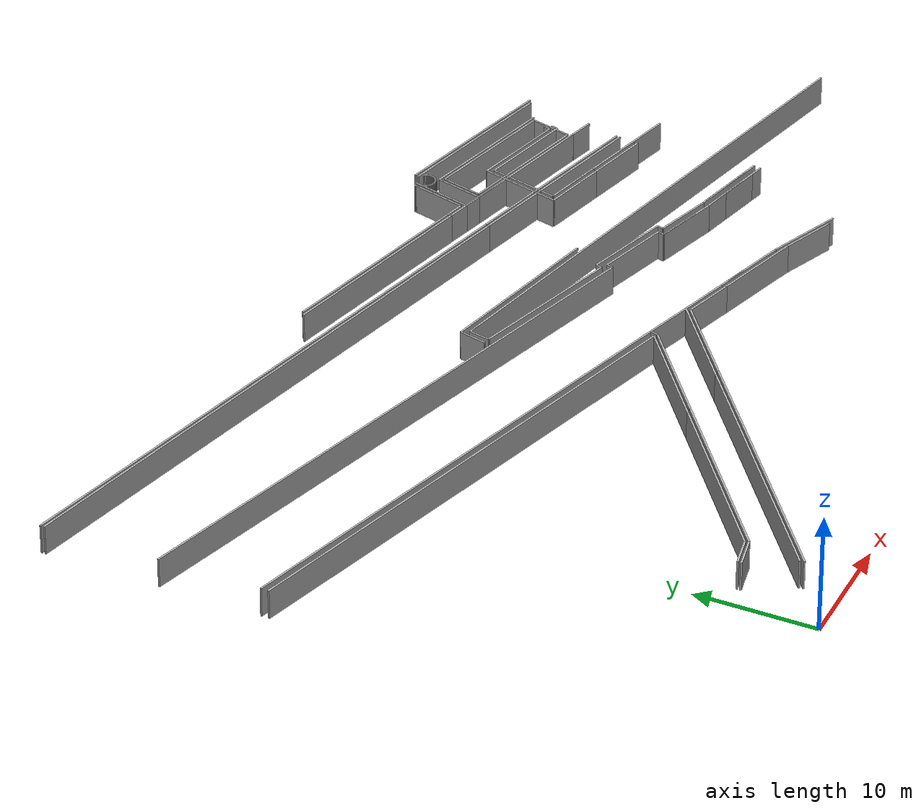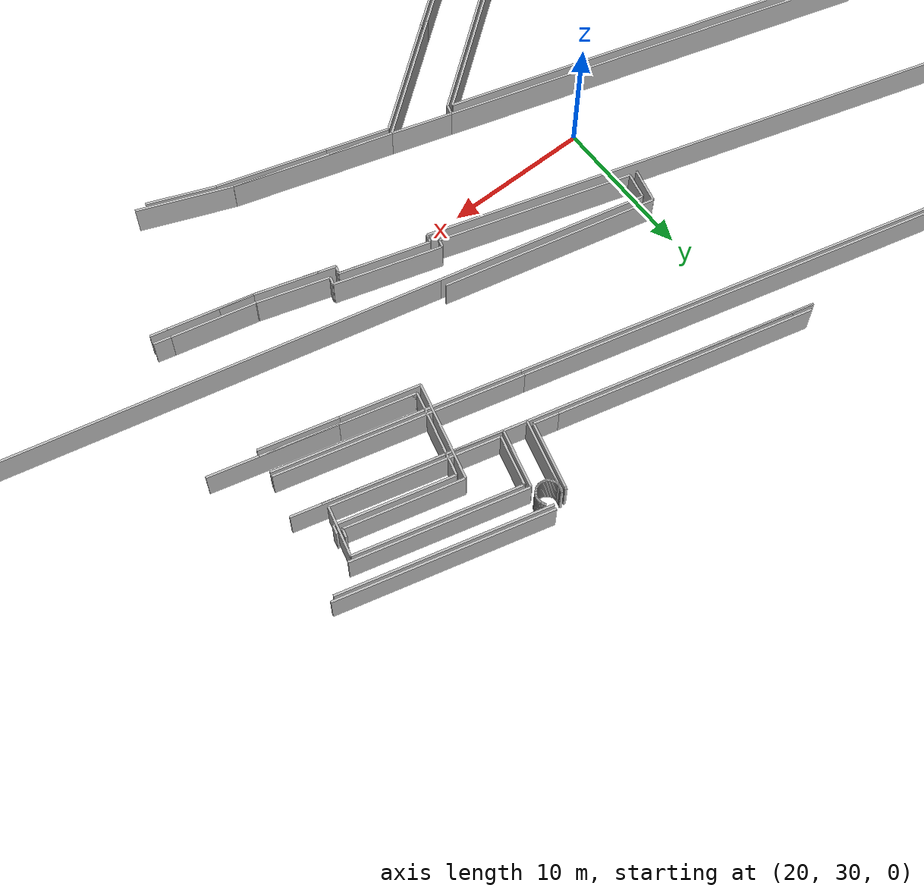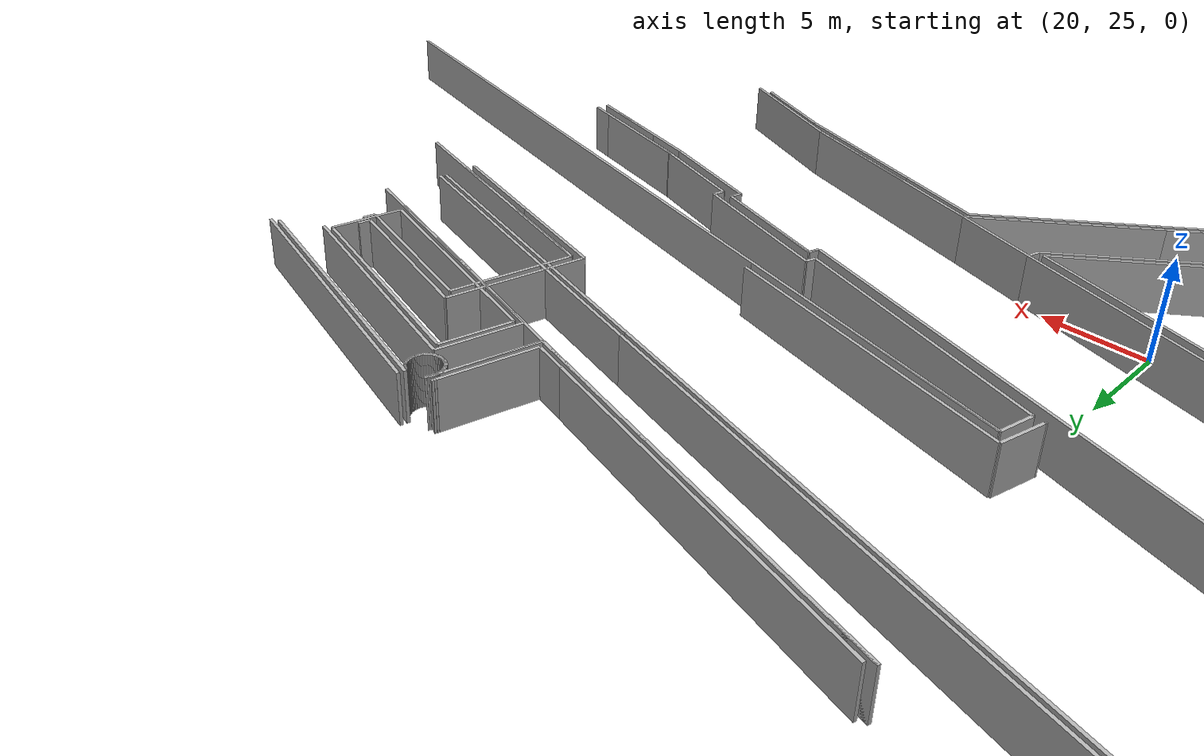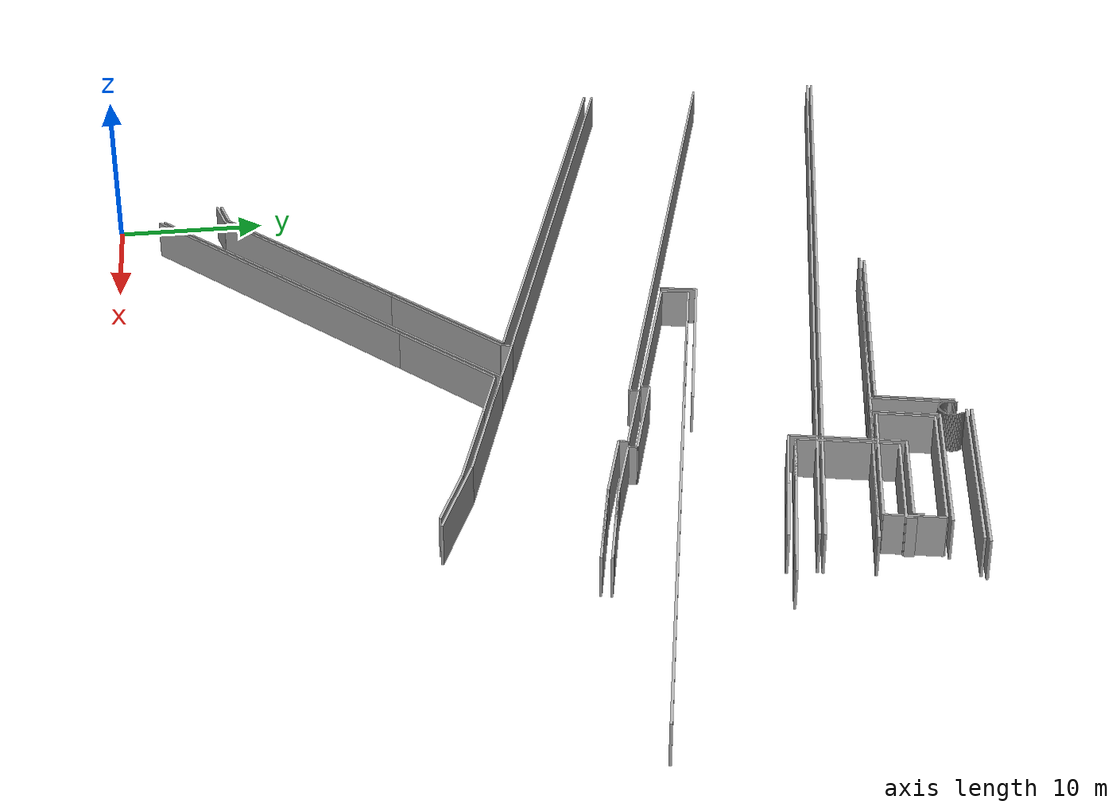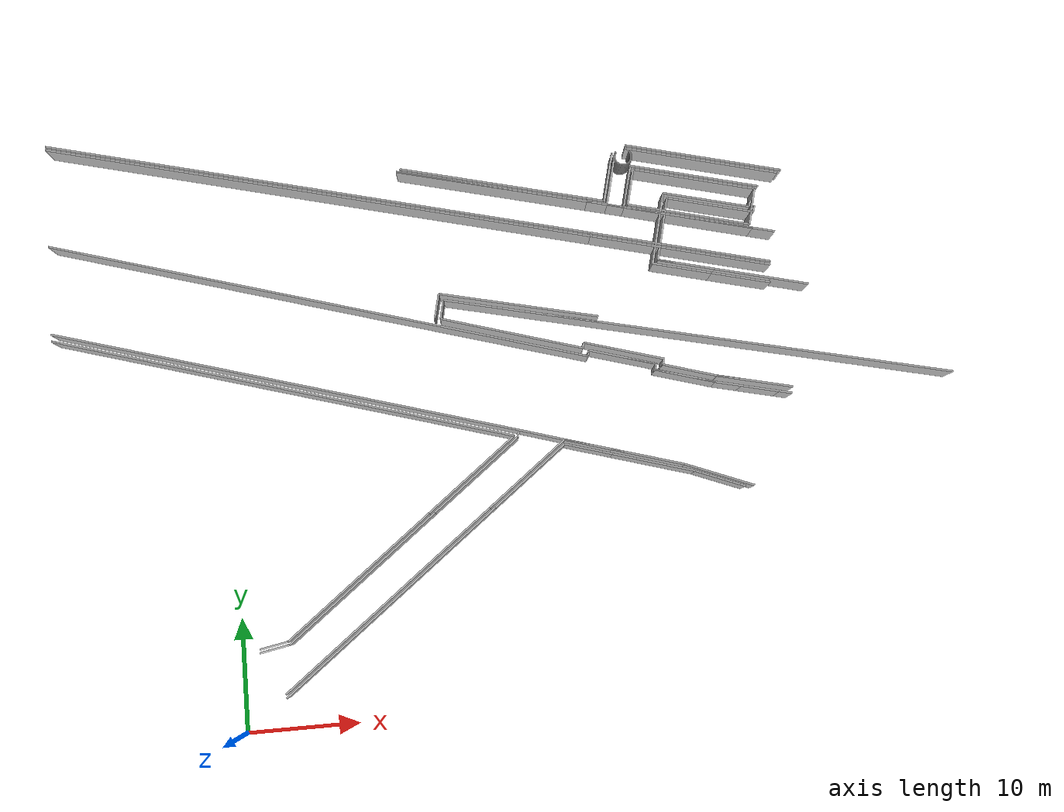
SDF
<?xml version="1.0" ?>
<sdf version="1.6">
  <model name="sps_0307">
    <pose frame="">0 0 0 0 -0 0</pose>
    <static>1</static>
    <self_collide>0</self_collide>
    <allow_auto_disable>0</allow_auto_disable>
    <link name="Wall47">
      <kinematic>0</kinematic>
      <gravity>1</gravity>
      <self_collide>0</self_collide>
      <collision name="collision">
        <geometry>
          <box>
            <size>2.31776 0.15 2.5</size>
          </box>
        </geometry>
        <pose frame="">0 0 0 0 -0 0</pose>
      </collision>
      <visual name="visual">
        <geometry>
          <box>
            <size>2.31776 0.15 2.5</size>
          </box>
        </geometry>
        <pose frame="">0 0 0 0 -0 0</pose>
        <cast_shadows>1</cast_shadows>
        <transparency>0.0</transparency>
      </visual>
      <pose frame="">19.8054 36.7291 1.25 0 0 -1.79919</pose>
    </link>
    <link name="Wall48">
      <kinematic>0</kinematic>
      <gravity>1</gravity>
      <self_collide>0</self_collide>
      <collision name="collision">
        <geometry>
          <box>
            <size>8.46473 0.15 2.5</size>
          </box>
        </geometry>
        <pose frame="">0 0 0 0 -0 0</pose>
      </collision>
      <visual name="visual">
        <geometry>
          <box>
            <size>8.46473 0.15 2.5</size>
          </box>
        </geometry>
        <pose frame="">0 0 0 0 -0 0</pose>
        <cast_shadows>1</cast_shadows>
        <transparency>0.0</transparency>
      </visual>
      <pose frame="">26.9262 20.4718 1.25 0 0 -2.48644</pose>
    </link>
    <link name="Wall49">
      <kinematic>0</kinematic>
      <gravity>1</gravity>
      <self_collide>0</self_collide>
      <collision name="collision">
        <geometry>
          <box>
            <size>24.6706 0.15 2.5</size>
          </box>
        </geometry>
        <pose frame="">0 0 0 0 -0 0</pose>
      </collision>
      <visual name="visual">
        <geometry>
          <box>
            <size>24.6706 0.15 2.5</size>
          </box>
        </geometry>
        <pose frame="">0 0 0 0 -0 0</pose>
        <cast_shadows>1</cast_shadows>
        <transparency>0.0</transparency>
      </visual>
      <pose frame="">13.7888 10.3774 1.25 0 0 -2.48644</pose>
    </link>
    <link name="Wall53">
      <kinematic>0</kinematic>
      <gravity>1</gravity>
      <self_collide>0</self_collide>
      <collision name="collision">
        <geometry>
          <box>
            <size>4.56991 0.15 2.5</size>
          </box>
        </geometry>
        <pose frame="">0 0 0 0 -0 0</pose>
      </collision>
      <visual name="visual">
        <geometry>
          <box>
            <size>4.56991 0.15 2.5</size>
          </box>
        </geometry>
        <pose frame="">0 0 0 0 -0 0</pose>
        <cast_shadows>1</cast_shadows>
        <transparency>0.0</transparency>
      </visual>
      <pose frame="">36.6741 47.5966 1.25 0 0 -1.82191</pose>
    </link>
    <link name="Wall57">
      <kinematic>0</kinematic>
      <gravity>1</gravity>
      <self_collide>0</self_collide>
      <collision name="collision">
        <geometry>
          <box>
            <size>4.36935 0.15 2.5</size>
          </box>
        </geometry>
        <pose frame="">0 0 0 0 -0 0</pose>
      </collision>
      <visual name="visual">
        <geometry>
          <box>
            <size>4.36935 0.15 2.5</size>
          </box>
        </geometry>
        <pose frame="">0 0 0 0 -0 0</pose>
        <cast_shadows>1</cast_shadows>
        <transparency>0.0</transparency>
      </visual>
      <pose frame="">32.3758 22.4263 1.25 0 0 -0.289769</pose>
    </link>
    <link name="Wall58">
      <kinematic>0</kinematic>
      <gravity>1</gravity>
      <self_collide>0</self_collide>
      <collision name="collision">
        <geometry>
          <box>
            <size>7.57833 0.15 2.5</size>
          </box>
        </geometry>
        <pose frame="">0 0 0 0 -0 0</pose>
      </collision>
      <visual name="visual">
        <geometry>
          <box>
            <size>7.57833 0.15 2.5</size>
          </box>
        </geometry>
        <pose frame="">0 0 0 0 -0 0</pose>
        <cast_shadows>1</cast_shadows>
        <transparency>0.0</transparency>
      </visual>
      <pose frame="">38.1006 20.7194 1.25 0 0 -0.289769</pose>
    </link>
    <link name="Wall62">
      <kinematic>0</kinematic>
      <gravity>1</gravity>
      <self_collide>0</self_collide>
      <collision name="collision">
        <geometry>
          <box>
            <size>11.4032 0.15 2.5</size>
          </box>
        </geometry>
        <pose frame="">0 0 0 0 -0 0</pose>
      </collision>
      <visual name="visual">
        <geometry>
          <box>
            <size>11.4032 0.15 2.5</size>
          </box>
        </geometry>
        <pose frame="">0 0 0 0 -0 0</pose>
        <cast_shadows>1</cast_shadows>
        <transparency>0.0</transparency>
      </visual>
      <pose frame="">44.6229 46.7845 1.25 0 -0 2.89098</pose>
    </link>
    <link name="Wall433">
      <kinematic>0</kinematic>
      <gravity>1</gravity>
      <self_collide>0</self_collide>
      <collision name="collision">
        <geometry>
          <box>
            <size>1.68756 0.15 2.5</size>
          </box>
        </geometry>
        <pose frame="">0 0 0 0 -0 0</pose>
      </collision>
      <visual name="visual">
        <geometry>
          <box>
            <size>1.68756 0.15 2.5</size>
          </box>
        </geometry>
        <pose frame="">0 0 0 0 -0 0</pose>
        <cast_shadows>1</cast_shadows>
        <transparency>0.0</transparency>
      </visual>
      <pose frame="">35.2879 45.5886 1.25 0 -0 2.89581</pose>
    </link>
    <link name="Wall434">
      <kinematic>0</kinematic>
      <gravity>1</gravity>
      <self_collide>0</self_collide>
      <collision name="collision">
        <geometry>
          <box>
            <size>17.6158 0.15 2.5</size>
          </box>
        </geometry>
        <pose frame="">0 0 0 0 -0 0</pose>
      </collision>
      <visual name="visual">
        <geometry>
          <box>
            <size>17.6158 0.15 2.5</size>
          </box>
        </geometry>
        <pose frame="">0 0 0 0 -0 0</pose>
        <cast_shadows>1</cast_shadows>
        <transparency>0.0</transparency>
      </visual>
      <pose frame="">25.9263 47.937 1.25 0 -0 2.89581</pose>
    </link>
    <link name="Wall442">
      <kinematic>0</kinematic>
      <gravity>1</gravity>
      <self_collide>0</self_collide>
      <collision name="collision">
        <geometry>
          <box>
            <size>3.47018 0.15 2.5</size>
          </box>
        </geometry>
        <pose frame="">0 0 0 0 -0 0</pose>
      </collision>
      <visual name="visual">
        <geometry>
          <box>
            <size>3.47018 0.15 2.5</size>
          </box>
        </geometry>
        <pose frame="">0 0 0 0 -0 0</pose>
        <cast_shadows>1</cast_shadows>
        <transparency>0.0</transparency>
      </visual>
      <pose frame="">49.7218 43.6882 1.25 0 -0 1.32352</pose>
    </link>
    <link name="Wall443">
      <kinematic>0</kinematic>
      <gravity>1</gravity>
      <self_collide>0</self_collide>
      <collision name="collision">
        <geometry>
          <box>
            <size>12.0027 0.15 2.5</size>
          </box>
        </geometry>
        <pose frame="">0 0 0 0 -0 0</pose>
      </collision>
      <visual name="visual">
        <geometry>
          <box>
            <size>12.0027 0.15 2.5</size>
          </box>
        </geometry>
        <pose frame="">0 0 0 0 -0 0</pose>
        <cast_shadows>1</cast_shadows>
        <transparency>0.0</transparency>
      </visual>
      <pose frame="">44.6974 47.0748 1.25 0 -0 2.89095</pose>
    </link>
    <link name="Wall444">
      <kinematic>0</kinematic>
      <gravity>1</gravity>
      <self_collide>0</self_collide>
      <collision name="collision">
        <geometry>
          <box>
            <size>16.884 0.15 2.5</size>
          </box>
        </geometry>
        <pose frame="">0 0 0 0 -0 0</pose>
      </collision>
      <visual name="visual">
        <geometry>
          <box>
            <size>16.884 0.15 2.5</size>
          </box>
        </geometry>
        <pose frame="">0 0 0 0 -0 0</pose>
        <cast_shadows>1</cast_shadows>
        <transparency>0.0</transparency>
      </visual>
      <pose frame="">42.6536 40.3847 1.25 0 -0 2.89383</pose>
    </link>
    <link name="Wall445">
      <kinematic>0</kinematic>
      <gravity>1</gravity>
      <self_collide>0</self_collide>
      <collision name="collision">
        <geometry>
          <box>
            <size>51.5749 0.15 2.5</size>
          </box>
        </geometry>
        <pose frame="">0 0 0 0 -0 0</pose>
      </collision>
      <visual name="visual">
        <geometry>
          <box>
            <size>51.5749 0.15 2.5</size>
          </box>
        </geometry>
        <pose frame="">0 0 0 0 -0 0</pose>
        <cast_shadows>1</cast_shadows>
        <transparency>0.0</transparency>
      </visual>
      <pose frame="">9.46944 48.7791 1.25 0 -0 2.89383</pose>
    </link>
    <link name="Wall456">
      <kinematic>0</kinematic>
      <gravity>1</gravity>
      <self_collide>0</self_collide>
      <collision name="collision">
        <geometry>
          <box>
            <size>6.51117 0.15 2.5</size>
          </box>
        </geometry>
        <pose frame="">0 0 0 0 -0 0</pose>
      </collision>
      <visual name="visual">
        <geometry>
          <box>
            <size>6.51117 0.15 2.5</size>
          </box>
        </geometry>
        <pose frame="">0 0 0 0 -0 0</pose>
        <cast_shadows>1</cast_shadows>
        <transparency>0.0</transparency>
      </visual>
      <pose frame="">43.8706 19.1032 1.25 0 0 -0.380844</pose>
    </link>
    <link name="Wall775">
      <kinematic>0</kinematic>
      <gravity>1</gravity>
      <self_collide>0</self_collide>
      <collision name="collision">
        <geometry>
          <box>
            <size>1.76737 0.15 2.5</size>
          </box>
        </geometry>
        <pose frame="">0 0 0 0 -0 0</pose>
      </collision>
      <visual name="visual">
        <geometry>
          <box>
            <size>1.76737 0.15 2.5</size>
          </box>
        </geometry>
        <pose frame="">0 0 0 0 -0 0</pose>
        <cast_shadows>1</cast_shadows>
        <transparency>0.0</transparency>
      </visual>
      <pose frame="">20.2484 36.3817 1.25 0 -0 1.35826</pose>
    </link>
    <link name="Wall776">
      <kinematic>0</kinematic>
      <gravity>1</gravity>
      <self_collide>0</self_collide>
      <collision name="collision">
        <geometry>
          <box>
            <size>17.1783 0.15 2.5</size>
          </box>
        </geometry>
        <pose frame="">0 0 0 0 -0 0</pose>
      </collision>
      <visual name="visual">
        <geometry>
          <box>
            <size>17.1783 0.15 2.5</size>
          </box>
        </geometry>
        <pose frame="">0 0 0 0 -0 0</pose>
        <cast_shadows>1</cast_shadows>
        <transparency>0.0</transparency>
      </visual>
      <pose frame="">11.3269 12.6561 1.25 0 -0 0.655713</pose>
    </link>
    <link name="Wall777">
      <kinematic>0</kinematic>
      <gravity>1</gravity>
      <self_collide>0</self_collide>
      <collision name="collision">
        <geometry>
          <box>
            <size>10.0645 0.15 2.5</size>
          </box>
        </geometry>
        <pose frame="">0 0 0 0 -0 0</pose>
      </collision>
      <visual name="visual">
        <geometry>
          <box>
            <size>10.0645 0.15 2.5</size>
          </box>
        </geometry>
        <pose frame="">0 0 0 0 -0 0</pose>
        <cast_shadows>1</cast_shadows>
        <transparency>0.0</transparency>
      </visual>
      <pose frame="">22.1234 20.9614 1.25 0 -0 0.655713</pose>
    </link>
    <link name="Wall778">
      <kinematic>0</kinematic>
      <gravity>1</gravity>
      <self_collide>0</self_collide>
      <collision name="collision">
        <geometry>
          <box>
            <size>9.12133 0.15 2.5</size>
          </box>
        </geometry>
        <pose frame="">0 0 0 0 -0 0</pose>
      </collision>
      <visual name="visual">
        <geometry>
          <box>
            <size>9.12133 0.15 2.5</size>
          </box>
        </geometry>
        <pose frame="">0 0 0 0 -0 0</pose>
        <cast_shadows>1</cast_shadows>
        <transparency>0.0</transparency>
      </visual>
      <pose frame="">26.6945 20.6718 1.25 0 0 -2.48644</pose>
    </link>
    <link name="Wall779">
      <kinematic>0</kinematic>
      <gravity>1</gravity>
      <self_collide>0</self_collide>
      <collision name="collision">
        <geometry>
          <box>
            <size>24.1272 0.15 2.5</size>
          </box>
        </geometry>
        <pose frame="">0 0 0 0 -0 0</pose>
      </collision>
      <visual name="visual">
        <geometry>
          <box>
            <size>24.1272 0.15 2.5</size>
          </box>
        </geometry>
        <pose frame="">0 0 0 0 -0 0</pose>
        <cast_shadows>1</cast_shadows>
        <transparency>0.0</transparency>
      </visual>
      <pose frame="">13.5122 10.543 1.25 0 0 -2.48644</pose>
    </link>
    <link name="Wall780">
      <kinematic>0</kinematic>
      <gravity>1</gravity>
      <self_collide>0</self_collide>
      <collision name="collision">
        <geometry>
          <box>
            <size>1.91084 0.15 2.5</size>
          </box>
        </geometry>
        <pose frame="">0 0 0 0 -0 0</pose>
      </collision>
      <visual name="visual">
        <geometry>
          <box>
            <size>1.91084 0.15 2.5</size>
          </box>
        </geometry>
        <pose frame="">0 0 0 0 -0 0</pose>
        <cast_shadows>1</cast_shadows>
        <transparency>0.0</transparency>
      </visual>
      <pose frame="">35.3961 45.2504 1.25 0 -0 2.89576</pose>
    </link>
    <link name="Wall781">
      <kinematic>0</kinematic>
      <gravity>1</gravity>
      <self_collide>0</self_collide>
      <collision name="collision">
        <geometry>
          <box>
            <size>17.9917 0.15 2.5</size>
          </box>
        </geometry>
        <pose frame="">0 0 0 0 -0 0</pose>
      </collision>
      <visual name="visual">
        <geometry>
          <box>
            <size>17.9917 0.15 2.5</size>
          </box>
        </geometry>
        <pose frame="">0 0 0 0 -0 0</pose>
        <cast_shadows>1</cast_shadows>
        <transparency>0.0</transparency>
      </visual>
      <pose frame="">25.744 47.6722 1.25 0 -0 2.89576</pose>
    </link>
    <link name="Wall782">
      <kinematic>0</kinematic>
      <gravity>1</gravity>
      <self_collide>0</self_collide>
      <collision name="collision">
        <geometry>
          <box>
            <size>3.47079 0.15 2.5</size>
          </box>
        </geometry>
        <pose frame="">0 0 0 0 -0 0</pose>
      </collision>
      <visual name="visual">
        <geometry>
          <box>
            <size>3.47079 0.15 2.5</size>
          </box>
        </geometry>
        <pose frame="">0 0 0 0 -0 0</pose>
        <cast_shadows>1</cast_shadows>
        <transparency>0.0</transparency>
      </visual>
      <pose frame="">38.6684 46.5175 1.25 0 0 -1.82184</pose>
    </link>
    <link name="Wall783">
      <kinematic>0</kinematic>
      <gravity>1</gravity>
      <self_collide>0</self_collide>
      <collision name="collision">
        <geometry>
          <box>
            <size>6.65549 0.15 2.5</size>
          </box>
        </geometry>
        <pose frame="">0 0 0 0 -0 0</pose>
      </collision>
      <visual name="visual">
        <geometry>
          <box>
            <size>6.65549 0.15 2.5</size>
          </box>
        </geometry>
        <pose frame="">0 0 0 0 -0 0</pose>
        <cast_shadows>1</cast_shadows>
        <transparency>0.0</transparency>
      </visual>
      <pose frame="">37.6588 21.2629 1.25 0 -0 2.85223</pose>
    </link>
    <link name="Wall784">
      <kinematic>0</kinematic>
      <gravity>1</gravity>
      <self_collide>0</self_collide>
      <collision name="collision">
        <geometry>
          <box>
            <size>4.33896 0.15 2.5</size>
          </box>
        </geometry>
        <pose frame="">0 0 0 0 -0 0</pose>
      </collision>
      <visual name="visual">
        <geometry>
          <box>
            <size>4.33896 0.15 2.5</size>
          </box>
        </geometry>
        <pose frame="">0 0 0 0 -0 0</pose>
        <cast_shadows>1</cast_shadows>
        <transparency>0.0</transparency>
      </visual>
      <pose frame="">32.3902 22.8315 1.25 0 -0 2.85223</pose>
    </link>
    <link name="Wall786">
      <kinematic>0</kinematic>
      <gravity>1</gravity>
      <self_collide>0</self_collide>
      <collision name="collision">
        <geometry>
          <box>
            <size>4.97067 0.15 2.5</size>
          </box>
        </geometry>
        <pose frame="">0 0 0 0 -0 0</pose>
      </collision>
      <visual name="visual">
        <geometry>
          <box>
            <size>4.97067 0.15 2.5</size>
          </box>
        </geometry>
        <pose frame="">0 0 0 0 -0 0</pose>
        <cast_shadows>1</cast_shadows>
        <transparency>0.0</transparency>
      </visual>
      <pose frame="">42.2593 28.8167 1.25 0 -0 2.84844</pose>
    </link>
    <link name="Wall790">
      <kinematic>0</kinematic>
      <gravity>1</gravity>
      <self_collide>0</self_collide>
      <collision name="collision">
        <geometry>
          <box>
            <size>51.575 0.15 2.5</size>
          </box>
        </geometry>
        <pose frame="">0 0 0 0 -0 0</pose>
      </collision>
      <visual name="visual">
        <geometry>
          <box>
            <size>51.575 0.15 2.5</size>
          </box>
        </geometry>
        <pose frame="">0 0 0 0 -0 0</pose>
        <cast_shadows>1</cast_shadows>
        <transparency>0.0</transparency>
      </visual>
      <pose frame="">9.46944 48.4692 1.25 0 0 -0.247766</pose>
    </link>
    <link name="Wall791">
      <kinematic>0</kinematic>
      <gravity>1</gravity>
      <self_collide>0</self_collide>
      <collision name="collision">
        <geometry>
          <box>
            <size>16.8081 0.15 2.5</size>
          </box>
        </geometry>
        <pose frame="">0 0 0 0 -0 0</pose>
      </collision>
      <visual name="visual">
        <geometry>
          <box>
            <size>16.8081 0.15 2.5</size>
          </box>
        </geometry>
        <pose frame="">0 0 0 0 -0 0</pose>
        <cast_shadows>1</cast_shadows>
        <transparency>0.0</transparency>
      </visual>
      <pose frame="">42.6168 40.0841 1.25 0 0 -0.247766</pose>
    </link>
    <link name="Wall792">
      <kinematic>0</kinematic>
      <gravity>1</gravity>
      <self_collide>0</self_collide>
      <collision name="collision">
        <geometry>
          <box>
            <size>15.7158 0.15 2.5</size>
          </box>
        </geometry>
        <pose frame="">0 0 0 0 -0 0</pose>
      </collision>
      <visual name="visual">
        <geometry>
          <box>
            <size>15.7158 0.15 2.5</size>
          </box>
        </geometry>
        <pose frame="">0 0 0 0 -0 0</pose>
        <cast_shadows>1</cast_shadows>
        <transparency>0.0</transparency>
      </visual>
      <pose frame="">43.9363 43.0715 1.25 0 0 -0.250307</pose>
    </link>
    <link name="Wall798">
      <kinematic>0</kinematic>
      <gravity>1</gravity>
      <self_collide>0</self_collide>
      <collision name="collision">
        <geometry>
          <box>
            <size>14.7851 0.15 2.5</size>
          </box>
        </geometry>
        <pose frame="">0 0 0 0 -0 0</pose>
      </collision>
      <visual name="visual">
        <geometry>
          <box>
            <size>14.7851 0.15 2.5</size>
          </box>
        </geometry>
        <pose frame="">0 0 0 0 -0 0</pose>
        <cast_shadows>1</cast_shadows>
        <transparency>0.0</transparency>
      </visual>
      <pose frame="">27.2686 36.1851 1.25 0 -0 2.91334</pose>
    </link>
    <link name="Wall1177">
      <kinematic>0</kinematic>
      <gravity>1</gravity>
      <self_collide>0</self_collide>
      <collision name="collision">
        <geometry>
          <box>
            <size>0.670105 0.15 2.5</size>
          </box>
        </geometry>
        <pose frame="">0 0 0 0 -0 0</pose>
      </collision>
      <visual name="visual">
        <geometry>
          <box>
            <size>0.670105 0.15 2.5</size>
          </box>
        </geometry>
        <pose frame="">0 0 0 0 -0 0</pose>
        <cast_shadows>1</cast_shadows>
        <transparency>0.0</transparency>
      </visual>
      <pose frame="">26.2098 24.3502 1.25 0 -0 1.27494</pose>
    </link>
    <link name="Wall1187">
      <kinematic>0</kinematic>
      <gravity>1</gravity>
      <self_collide>0</self_collide>
      <collision name="collision">
        <geometry>
          <box>
            <size>14.6975 0.15 2.5</size>
          </box>
        </geometry>
        <pose frame="">0 0 0 0 -0 0</pose>
      </collision>
      <visual name="visual">
        <geometry>
          <box>
            <size>14.6975 0.15 2.5</size>
          </box>
        </geometry>
        <pose frame="">0 0 0 0 -0 0</pose>
        <cast_shadows>1</cast_shadows>
        <transparency>0.0</transparency>
      </visual>
      <pose frame="">45.7006 48.7817 1.25 0 -0 2.89127</pose>
    </link>
    <link name="Wall1497">
      <kinematic>0</kinematic>
      <gravity>1</gravity>
      <self_collide>0</self_collide>
      <collision name="collision">
        <geometry>
          <box>
            <size>2.67232 0.15 2.5</size>
          </box>
        </geometry>
        <pose frame="">0 0 0 0 -0 0</pose>
      </collision>
      <visual name="visual">
        <geometry>
          <box>
            <size>2.67232 0.15 2.5</size>
          </box>
        </geometry>
        <pose frame="">0 0 0 0 -0 0</pose>
        <cast_shadows>1</cast_shadows>
        <transparency>0.0</transparency>
      </visual>
      <pose frame="">3.20547 7.17457 1.25 0 -0 0.184029</pose>
    </link>
    <link name="Wall1501">
      <kinematic>0</kinematic>
      <gravity>1</gravity>
      <self_collide>0</self_collide>
      <collision name="collision">
        <geometry>
          <box>
            <size>13.2712 0.15 2.5</size>
          </box>
        </geometry>
        <pose frame="">0 0 0 0 -0 0</pose>
      </collision>
      <visual name="visual">
        <geometry>
          <box>
            <size>13.2712 0.15 2.5</size>
          </box>
        </geometry>
        <pose frame="">0 0 0 0 -0 0</pose>
        <cast_shadows>1</cast_shadows>
        <transparency>0.0</transparency>
      </visual>
      <pose frame="">26.4145 33.6001 1.25 0 -0 2.84839</pose>
    </link>
    <link name="Wall1503">
      <kinematic>0</kinematic>
      <gravity>1</gravity>
      <self_collide>0</self_collide>
      <collision name="collision">
        <geometry>
          <box>
            <size>4.8703 0.15 2.5</size>
          </box>
        </geometry>
        <pose frame="">0 0 0 0 -0 0</pose>
      </collision>
      <visual name="visual">
        <geometry>
          <box>
            <size>4.8703 0.15 2.5</size>
          </box>
        </geometry>
        <pose frame="">0 0 0 0 -0 0</pose>
        <cast_shadows>1</cast_shadows>
        <transparency>0.0</transparency>
      </visual>
      <pose frame="">36.9278 47.3767 1.25 0 0 -1.82188</pose>
    </link>
    <link name="Wall1506">
      <kinematic>0</kinematic>
      <gravity>1</gravity>
      <self_collide>0</self_collide>
      <collision name="collision">
        <geometry>
          <box>
            <size>5.54428 0.15 2.5</size>
          </box>
        </geometry>
        <pose frame="">0 0 0 0 -0 0</pose>
      </collision>
      <visual name="visual">
        <geometry>
          <box>
            <size>5.54428 0.15 2.5</size>
          </box>
        </geometry>
        <pose frame="">0 0 0 0 -0 0</pose>
        <cast_shadows>1</cast_shadows>
        <transparency>0.0</transparency>
      </visual>
      <pose frame="">41.7877 28.3312 1.25 0 0 -0.289481</pose>
    </link>
    <link name="Wall1796">
      <kinematic>0</kinematic>
      <gravity>1</gravity>
      <self_collide>0</self_collide>
      <collision name="collision">
        <geometry>
          <box>
            <size>16.7154 0.15 2.5</size>
          </box>
        </geometry>
        <pose frame="">0 0 0 0 -0 0</pose>
      </collision>
      <visual name="visual">
        <geometry>
          <box>
            <size>16.7154 0.15 2.5</size>
          </box>
        </geometry>
        <pose frame="">0 0 0 0 -0 0</pose>
        <cast_shadows>1</cast_shadows>
        <transparency>0.0</transparency>
      </visual>
      <pose frame="">11.0183 12.797 1.25 0 -0 0.655744</pose>
    </link>
    <link name="Wall1797">
      <kinematic>0</kinematic>
      <gravity>1</gravity>
      <self_collide>0</self_collide>
      <collision name="collision">
        <geometry>
          <box>
            <size>10.3269 0.15 2.5</size>
          </box>
        </geometry>
        <pose frame="">0 0 0 0 -0 0</pose>
      </collision>
      <visual name="visual">
        <geometry>
          <box>
            <size>10.3269 0.15 2.5</size>
          </box>
        </geometry>
        <pose frame="">0 0 0 0 -0 0</pose>
        <cast_shadows>1</cast_shadows>
        <transparency>0.0</transparency>
      </visual>
      <pose frame="">21.7351 21.0415 1.25 0 -0 0.655744</pose>
    </link>
    <link name="Wall1799">
      <kinematic>0</kinematic>
      <gravity>1</gravity>
      <self_collide>0</self_collide>
      <collision name="collision">
        <geometry>
          <box>
            <size>43.64 0.15 2.5</size>
          </box>
        </geometry>
        <pose frame="">0 0 0 0 -0 0</pose>
      </collision>
      <visual name="visual">
        <geometry>
          <box>
            <size>43.64 0.15 2.5</size>
          </box>
        </geometry>
        <pose frame="">0 0 0 0 -0 0</pose>
        <cast_shadows>1</cast_shadows>
        <transparency>0.0</transparency>
      </visual>
      <pose frame="">5.38845 30.8761 1.25 0 0 -0.288371</pose>
    </link>
    <link name="Wall1813">
      <kinematic>0</kinematic>
      <gravity>1</gravity>
      <self_collide>0</self_collide>
      <collision name="collision">
        <geometry>
          <box>
            <size>4.6907 0.15 2.5</size>
          </box>
        </geometry>
        <pose frame="">0 0 0 0 -0 0</pose>
      </collision>
      <visual name="visual">
        <geometry>
          <box>
            <size>4.6907 0.15 2.5</size>
          </box>
        </geometry>
        <pose frame="">0 0 0 0 -0 0</pose>
        <cast_shadows>1</cast_shadows>
        <transparency>0.0</transparency>
      </visual>
      <pose frame="">43.9091 18.7649 1.25 0 0 -0.380853</pose>
    </link>
    <link name="Wall2140">
      <kinematic>0</kinematic>
      <gravity>1</gravity>
      <self_collide>0</self_collide>
      <collision name="collision">
        <geometry>
          <box>
            <size>11.4163 0.15 2.5</size>
          </box>
        </geometry>
        <pose frame="">0 0 0 0 -0 0</pose>
      </collision>
      <visual name="visual">
        <geometry>
          <box>
            <size>11.4163 0.15 2.5</size>
          </box>
        </geometry>
        <pose frame="">0 0 0 0 -0 0</pose>
        <cast_shadows>1</cast_shadows>
        <transparency>0.0</transparency>
      </visual>
      <pose frame="">43.7672 43.4212 1.25 0 0 -0.25056</pose>
    </link>
    <link name="Wall2142">
      <kinematic>0</kinematic>
      <gravity>1</gravity>
      <self_collide>0</self_collide>
      <collision name="collision">
        <geometry>
          <box>
            <size>6.96064 0.15 2.5</size>
          </box>
        </geometry>
        <pose frame="">0 0 0 0 -0 0</pose>
      </collision>
      <visual name="visual">
        <geometry>
          <box>
            <size>6.96064 0.15 2.5</size>
          </box>
        </geometry>
        <pose frame="">0 0 0 0 -0 0</pose>
        <cast_shadows>1</cast_shadows>
        <transparency>0.0</transparency>
      </visual>
      <pose frame="">48.0266 27.3022 1.25 0 0 -0.230844</pose>
    </link>
    <link name="Wall2150">
      <kinematic>0</kinematic>
      <gravity>1</gravity>
      <self_collide>0</self_collide>
      <collision name="collision">
        <geometry>
          <box>
            <size>14.4073 0.15 2.5</size>
          </box>
        </geometry>
        <pose frame="">0 0 0 0 -0 0</pose>
      </collision>
      <visual name="visual">
        <geometry>
          <box>
            <size>14.4073 0.15 2.5</size>
          </box>
        </geometry>
        <pose frame="">0 0 0 0 -0 0</pose>
        <cast_shadows>1</cast_shadows>
        <transparency>0.0</transparency>
      </visual>
      <pose frame="">27.4521 35.6176 1.25 0 -0 2.91364</pose>
    </link>
    <link name="Wall2516">
      <kinematic>0</kinematic>
      <gravity>1</gravity>
      <self_collide>0</self_collide>
      <collision name="collision">
        <geometry>
          <box>
            <size>2.52876 0.15 2.5</size>
          </box>
        </geometry>
        <pose frame="">0 0 0 0 -0 0</pose>
      </collision>
      <visual name="visual">
        <geometry>
          <box>
            <size>2.52876 0.15 2.5</size>
          </box>
        </geometry>
        <pose frame="">0 0 0 0 -0 0</pose>
        <cast_shadows>1</cast_shadows>
        <transparency>0.0</transparency>
      </visual>
      <pose frame="">3.15096 7.46989 1.25 0 -0 0.18372</pose>
    </link>
    <link name="Wall2520">
      <kinematic>0</kinematic>
      <gravity>1</gravity>
      <self_collide>0</self_collide>
      <collision name="collision">
        <geometry>
          <box>
            <size>43.1391 0.15 2.5</size>
          </box>
        </geometry>
        <pose frame="">0 0 0 0 -0 0</pose>
      </collision>
      <visual name="visual">
        <geometry>
          <box>
            <size>43.1391 0.15 2.5</size>
          </box>
        </geometry>
        <pose frame="">0 0 0 0 -0 0</pose>
        <cast_shadows>1</cast_shadows>
        <transparency>0.0</transparency>
      </visual>
      <pose frame="">5.14855 30.3234 1.25 0 0 -0.288338</pose>
    </link>
    <link name="Wall2523">
      <kinematic>0</kinematic>
      <gravity>1</gravity>
      <self_collide>0</self_collide>
      <collision name="collision">
        <geometry>
          <box>
            <size>50.8037 0.15 2.5</size>
          </box>
        </geometry>
        <pose frame="">0 0 0 0 -0 0</pose>
      </collision>
      <visual name="visual">
        <geometry>
          <box>
            <size>50.8037 0.15 2.5</size>
          </box>
        </geometry>
        <pose frame="">0 0 0 0 -0 0</pose>
        <cast_shadows>1</cast_shadows>
        <transparency>0.0</transparency>
      </visual>
      <pose frame="">8.81466 38.1509 1.25 0 0 -0.289445</pose>
    </link>
    <link name="Wall2526">
      <kinematic>0</kinematic>
      <gravity>1</gravity>
      <self_collide>0</self_collide>
      <collision name="collision">
        <geometry>
          <box>
            <size>4.07023 0.15 2.5</size>
          </box>
        </geometry>
        <pose frame="">0 0 0 0 -0 0</pose>
      </collision>
      <visual name="visual">
        <geometry>
          <box>
            <size>4.07023 0.15 2.5</size>
          </box>
        </geometry>
        <pose frame="">0 0 0 0 -0 0</pose>
        <cast_shadows>1</cast_shadows>
        <transparency>0.0</transparency>
      </visual>
      <pose frame="">38.378 46.592 1.25 0 0 -1.82186</pose>
    </link>
    <link name="Wall2530">
      <kinematic>0</kinematic>
      <gravity>1</gravity>
      <self_collide>0</self_collide>
      <collision name="collision">
        <geometry>
          <box>
            <size>12.0166 0.15 2.5</size>
          </box>
        </geometry>
        <pose frame="">0 0 0 0 -0 0</pose>
      </collision>
      <visual name="visual">
        <geometry>
          <box>
            <size>12.0166 0.15 2.5</size>
          </box>
        </geometry>
        <pose frame="">0 0 0 0 -0 0</pose>
        <cast_shadows>1</cast_shadows>
        <transparency>0.0</transparency>
      </visual>
      <pose frame="">43.693 43.1306 1.25 0 0 -0.25062</pose>
    </link>
    <link name="Wall2533">
      <kinematic>0</kinematic>
      <gravity>1</gravity>
      <self_collide>0</self_collide>
      <collision name="collision">
        <geometry>
          <box>
            <size>7.02095 0.15 2.5</size>
          </box>
        </geometry>
        <pose frame="">0 0 0 0 -0 0</pose>
      </collision>
      <visual name="visual">
        <geometry>
          <box>
            <size>7.02095 0.15 2.5</size>
          </box>
        </geometry>
        <pose frame="">0 0 0 0 -0 0</pose>
        <cast_shadows>1</cast_shadows>
        <transparency>0.0</transparency>
      </visual>
      <pose frame="">47.8605 26.7309 1.25 0 -0 2.90905</pose>
    </link>
    <link name="Wall2536">
      <kinematic>0</kinematic>
      <gravity>1</gravity>
      <self_collide>0</self_collide>
      <collision name="collision">
        <geometry>
          <box>
            <size>14.3982 0.15 2.5</size>
          </box>
        </geometry>
        <pose frame="">0 0 0 0 -0 0</pose>
      </collision>
      <visual name="visual">
        <geometry>
          <box>
            <size>14.3982 0.15 2.5</size>
          </box>
        </geometry>
        <pose frame="">0 0 0 0 -0 0</pose>
        <cast_shadows>1</cast_shadows>
        <transparency>0.0</transparency>
      </visual>
      <pose frame="">45.4809 48.5276 1.25 0 0 -0.250347</pose>
    </link>
    <link name="Wall2859">
      <kinematic>0</kinematic>
      <gravity>1</gravity>
      <self_collide>0</self_collide>
      <collision name="collision">
        <geometry>
          <box>
            <size>5.77967 0.15 2.5</size>
          </box>
        </geometry>
        <pose frame="">0 0 0 0 -0 0</pose>
      </collision>
      <visual name="visual">
        <geometry>
          <box>
            <size>5.77967 0.15 2.5</size>
          </box>
        </geometry>
        <pose frame="">0 0 0 0 -0 0</pose>
        <cast_shadows>1</cast_shadows>
        <transparency>0.0</transparency>
      </visual>
      <pose frame="">47.452 27.4383 1.25 0 -0 2.91111</pose>
    </link>
    <link name="Wall2860">
      <kinematic>0</kinematic>
      <gravity>1</gravity>
      <self_collide>0</self_collide>
      <collision name="collision">
        <geometry>
          <box>
            <size>4.97067 0.15 2.5</size>
          </box>
        </geometry>
        <pose frame="">0 0 0 0 -0 0</pose>
      </collision>
      <visual name="visual">
        <geometry>
          <box>
            <size>4.97067 0.15 2.5</size>
          </box>
        </geometry>
        <pose frame="">0 0 0 0 -0 0</pose>
        <cast_shadows>1</cast_shadows>
        <transparency>0.0</transparency>
      </visual>
      <pose frame="">42.2593 28.8167 1.25 0 -0 2.84844</pose>
    </link>
    <link name="Wall2861">
      <kinematic>0</kinematic>
      <gravity>1</gravity>
      <self_collide>0</self_collide>
      <collision name="collision">
        <geometry>
          <box>
            <size>0.540889 0.15 2.5</size>
          </box>
        </geometry>
        <pose frame="">0 0 0 0 -0 0</pose>
      </collision>
      <visual name="visual">
        <geometry>
          <box>
            <size>0.540889 0.15 2.5</size>
          </box>
        </geometry>
        <pose frame="">0 0 0 0 -0 0</pose>
        <cast_shadows>1</cast_shadows>
        <transparency>0.0</transparency>
      </visual>
      <pose frame="">39.9571 29.7941 1.25 0 -0 1.28163</pose>
    </link>
    <link name="Wall2862">
      <kinematic>0</kinematic>
      <gravity>1</gravity>
      <self_collide>0</self_collide>
      <collision name="collision">
        <geometry>
          <box>
            <size>7.43031 0.15 2.5</size>
          </box>
        </geometry>
        <pose frame="">0 0 0 0 -0 0</pose>
      </collision>
      <visual name="visual">
        <geometry>
          <box>
            <size>7.43031 0.15 2.5</size>
          </box>
        </geometry>
        <pose frame="">0 0 0 0 -0 0</pose>
        <cast_shadows>1</cast_shadows>
        <transparency>0.0</transparency>
      </visual>
      <pose frame="">36.4737 31.1137 1.25 0 -0 2.85214</pose>
    </link>
    <link name="Wall2863">
      <kinematic>0</kinematic>
      <gravity>1</gravity>
      <self_collide>0</self_collide>
      <collision name="collision">
        <geometry>
          <box>
            <size>0.513085 0.15 2.5</size>
          </box>
        </geometry>
        <pose frame="">0 0 0 0 -0 0</pose>
      </collision>
      <visual name="visual">
        <geometry>
          <box>
            <size>0.513085 0.15 2.5</size>
          </box>
        </geometry>
        <pose frame="">0 0 0 0 -0 0</pose>
        <cast_shadows>1</cast_shadows>
        <transparency>0.0</transparency>
      </visual>
      <pose frame="">32.84 31.9282 1.25 0 0 -1.8597</pose>
    </link>
    <link name="Wall2864">
      <kinematic>0</kinematic>
      <gravity>1</gravity>
      <self_collide>0</self_collide>
      <collision name="collision">
        <geometry>
          <box>
            <size>13.2712 0.15 2.5</size>
          </box>
        </geometry>
        <pose frame="">0 0 0 0 -0 0</pose>
      </collision>
      <visual name="visual">
        <geometry>
          <box>
            <size>13.2712 0.15 2.5</size>
          </box>
        </geometry>
        <pose frame="">0 0 0 0 -0 0</pose>
        <cast_shadows>1</cast_shadows>
        <transparency>0.0</transparency>
      </visual>
      <pose frame="">26.4145 33.6001 1.25 0 -0 2.84839</pose>
    </link>
    <link name="Wall2865">
      <kinematic>0</kinematic>
      <gravity>1</gravity>
      <self_collide>0</self_collide>
      <collision name="collision">
        <geometry>
          <box>
            <size>1.76737 0.15 2.5</size>
          </box>
        </geometry>
        <pose frame="">0 0 0 0 -0 0</pose>
      </collision>
      <visual name="visual">
        <geometry>
          <box>
            <size>1.76737 0.15 2.5</size>
          </box>
        </geometry>
        <pose frame="">0 0 0 0 -0 0</pose>
        <cast_shadows>1</cast_shadows>
        <transparency>0.0</transparency>
      </visual>
      <pose frame="">20.2484 36.3817 1.25 0 -0 1.35826</pose>
    </link>
    <link name="Wall2866">
      <kinematic>0</kinematic>
      <gravity>1</gravity>
      <self_collide>0</self_collide>
      <collision name="collision">
        <geometry>
          <box>
            <size>46.875 0.15 2.5</size>
          </box>
        </geometry>
        <pose frame="">0 0 0 0 -0 0</pose>
      </collision>
      <visual name="visual">
        <geometry>
          <box>
            <size>46.875 0.15 2.5</size>
          </box>
        </geometry>
        <pose frame="">0 0 0 0 -0 0</pose>
        <cast_shadows>1</cast_shadows>
        <transparency>0.0</transparency>
      </visual>
      <pose frame="">43.266 31.949 1.25 0 0 -0.227953</pose>
    </link>
    <link name="Wall3020">
      <kinematic>0</kinematic>
      <gravity>1</gravity>
      <self_collide>0</self_collide>
      <collision name="collision">
        <geometry>
          <box>
            <size>10.9945 0.15 2.5</size>
          </box>
        </geometry>
        <pose frame="">0 0 0 0 -0 0</pose>
      </collision>
      <visual name="visual">
        <geometry>
          <box>
            <size>10.9945 0.15 2.5</size>
          </box>
        </geometry>
        <pose frame="">0 0 0 0 -0 0</pose>
        <cast_shadows>1</cast_shadows>
        <transparency>0.0</transparency>
      </visual>
      <pose frame="">35.5799 21.882 1.25 0 -0 2.85224</pose>
    </link>
    <link name="Wall3021">
      <kinematic>0</kinematic>
      <gravity>1</gravity>
      <self_collide>0</self_collide>
      <collision name="collision">
        <geometry>
          <box>
            <size>4.1854 0.15 2.5</size>
          </box>
        </geometry>
        <pose frame="">0 0 0 0 -0 0</pose>
      </collision>
      <visual name="visual">
        <geometry>
          <box>
            <size>4.1854 0.15 2.5</size>
          </box>
        </geometry>
        <pose frame="">0 0 0 0 -0 0</pose>
        <cast_shadows>1</cast_shadows>
        <transparency>0.0</transparency>
      </visual>
      <pose frame="">28.3094 24.0606 1.25 0 -0 2.84577</pose>
    </link>
    <link name="Wall3025">
      <kinematic>0</kinematic>
      <gravity>1</gravity>
      <self_collide>0</self_collide>
      <collision name="collision">
        <geometry>
          <box>
            <size>0.54988 0.15 2.5</size>
          </box>
        </geometry>
        <pose frame="">0 0 0 0 -0 0</pose>
      </collision>
      <visual name="visual">
        <geometry>
          <box>
            <size>0.54988 0.15 2.5</size>
          </box>
        </geometry>
        <pose frame="">0 0 0 0 -0 0</pose>
        <cast_shadows>1</cast_shadows>
        <transparency>0.0</transparency>
      </visual>
      <pose frame="">33.2388 31.1644 1.25 0 -0 1.28117</pose>
    </link>
    <link name="Wall3026">
      <kinematic>0</kinematic>
      <gravity>1</gravity>
      <self_collide>0</self_collide>
      <collision name="collision">
        <geometry>
          <box>
            <size>6.23016 0.15 2.5</size>
          </box>
        </geometry>
        <pose frame="">0 0 0 0 -0 0</pose>
      </collision>
      <visual name="visual">
        <geometry>
          <box>
            <size>6.23016 0.15 2.5</size>
          </box>
        </geometry>
        <pose frame="">0 0 0 0 -0 0</pose>
        <cast_shadows>1</cast_shadows>
        <transparency>0.0</transparency>
      </visual>
      <pose frame="">36.3028 30.5387 1.25 0 0 -0.289473</pose>
    </link>
    <link name="Wall3027">
      <kinematic>0</kinematic>
      <gravity>1</gravity>
      <self_collide>0</self_collide>
      <collision name="collision">
        <geometry>
          <box>
            <size>0.549863 0.15 2.5</size>
          </box>
        </geometry>
        <pose frame="">0 0 0 0 -0 0</pose>
      </collision>
      <visual name="visual">
        <geometry>
          <box>
            <size>0.549863 0.15 2.5</size>
          </box>
        </geometry>
        <pose frame="">0 0 0 0 -0 0</pose>
        <cast_shadows>1</cast_shadows>
        <transparency>0.0</transparency>
      </visual>
      <pose frame="">39.2097 29.386 1.25 0 0 -1.86032</pose>
    </link>
    <link name="Wall3028">
      <kinematic>0</kinematic>
      <gravity>1</gravity>
      <self_collide>0</self_collide>
      <collision name="collision">
        <geometry>
          <box>
            <size>5.54428 0.15 2.5</size>
          </box>
        </geometry>
        <pose frame="">0 0 0 0 -0 0</pose>
      </collision>
      <visual name="visual">
        <geometry>
          <box>
            <size>5.54428 0.15 2.5</size>
          </box>
        </geometry>
        <pose frame="">0 0 0 0 -0 0</pose>
        <cast_shadows>1</cast_shadows>
        <transparency>0.0</transparency>
      </visual>
      <pose frame="">41.788 28.3312 1.25 0 0 -0.289481</pose>
    </link>
    <link name="Wall3029">
      <kinematic>0</kinematic>
      <gravity>1</gravity>
      <self_collide>0</self_collide>
      <collision name="collision">
        <geometry>
          <box>
            <size>5.84084 0.15 2.5</size>
          </box>
        </geometry>
        <pose frame="">0 0 0 0 -0 0</pose>
      </collision>
      <visual name="visual">
        <geometry>
          <box>
            <size>5.84084 0.15 2.5</size>
          </box>
        </geometry>
        <pose frame="">0 0 0 0 -0 0</pose>
        <cast_shadows>1</cast_shadows>
        <transparency>0.0</transparency>
      </visual>
      <pose frame="">47.2866 26.8668 1.25 0 0 -0.23257</pose>
    </link>
    <link name="Wall4654">
      <kinematic>0</kinematic>
      <gravity>1</gravity>
      <self_collide>0</self_collide>
      <collision name="collision">
        <geometry>
          <box>
            <size>19.903 0.15 2.5</size>
          </box>
        </geometry>
        <pose frame="">0 0 0 0 -0 0</pose>
      </collision>
      <visual name="visual">
        <geometry>
          <box>
            <size>19.903 0.15 2.5</size>
          </box>
        </geometry>
        <pose frame="">0 0 0 0 -0 0</pose>
        <cast_shadows>1</cast_shadows>
        <transparency>0.0</transparency>
      </visual>
      <pose frame="">26.671 47.4397 1.25 0 0 -0.245827</pose>
    </link>
    <link name="Wall4655">
      <kinematic>0</kinematic>
      <gravity>1</gravity>
      <self_collide>0</self_collide>
      <collision name="collision">
        <geometry>
          <box>
            <size>4.87028 0.15 2.5</size>
          </box>
        </geometry>
        <pose frame="">0 0 0 0 -0 0</pose>
      </collision>
      <visual name="visual">
        <geometry>
          <box>
            <size>4.87028 0.15 2.5</size>
          </box>
        </geometry>
        <pose frame="">0 0 0 0 -0 0</pose>
        <cast_shadows>1</cast_shadows>
        <transparency>0.0</transparency>
      </visual>
      <pose frame="">36.9282 47.3767 1.25 0 -0 1.31973</pose>
    </link>
    <link name="Wall4657">
      <kinematic>0</kinematic>
      <gravity>1</gravity>
      <self_collide>0</self_collide>
      <collision name="collision">
        <geometry>
          <box>
            <size>14.3982 0.15 2.5</size>
          </box>
        </geometry>
        <pose frame="">0 0 0 0 -0 0</pose>
      </collision>
      <visual name="visual">
        <geometry>
          <box>
            <size>14.3982 0.15 2.5</size>
          </box>
        </geometry>
        <pose frame="">0 0 0 0 -0 0</pose>
        <cast_shadows>1</cast_shadows>
        <transparency>0.0</transparency>
      </visual>
      <pose frame="">45.4809 48.5276 1.25 0 0 -0.250347</pose>
    </link>
    <link name="Wall5722">
      <kinematic>0</kinematic>
      <gravity>1</gravity>
      <self_collide>0</self_collide>
      <collision name="collision">
        <geometry>
          <box>
            <size>19.9028 0.15 2.5</size>
          </box>
        </geometry>
        <pose frame="">0 0 0 0 -0 0</pose>
      </collision>
      <visual name="visual">
        <geometry>
          <box>
            <size>19.9028 0.15 2.5</size>
          </box>
        </geometry>
        <pose frame="">0 0 0 0 -0 0</pose>
        <cast_shadows>1</cast_shadows>
        <transparency>0.0</transparency>
      </visual>
      <pose frame="">26.6709 47.4397 1.25 0 0 -0.24583</pose>
    </link>
    <link name="Wall5723">
      <kinematic>0</kinematic>
      <gravity>1</gravity>
      <self_collide>0</self_collide>
      <collision name="collision">
        <geometry>
          <box>
            <size>1.59948 0.15 2.5</size>
          </box>
        </geometry>
        <pose frame="">0 0 0 0 -0 0</pose>
      </collision>
      <visual name="visual">
        <geometry>
          <box>
            <size>1.59948 0.15 2.5</size>
          </box>
        </geometry>
        <pose frame="">0 0 0 0 -0 0</pose>
        <cast_shadows>1</cast_shadows>
        <transparency>0.0</transparency>
      </visual>
      <pose frame="">37.0978 44.8193 1.25 0 0 -0.250967</pose>
    </link>
    <link name="Wall5724">
      <kinematic>0</kinematic>
      <gravity>1</gravity>
      <self_collide>0</self_collide>
      <collision name="collision">
        <geometry>
          <box>
            <size>3.39581 0.15 2.5</size>
          </box>
        </geometry>
        <pose frame="">0 0 0 0 -0 0</pose>
      </collision>
      <visual name="visual">
        <geometry>
          <box>
            <size>3.39581 0.15 2.5</size>
          </box>
        </geometry>
        <pose frame="">0 0 0 0 -0 0</pose>
        <cast_shadows>1</cast_shadows>
        <transparency>0.0</transparency>
      </visual>
      <pose frame="">39.5174 44.2001 1.25 0 0 -0.250319</pose>
    </link>
    <link name="Wall5725">
      <kinematic>0</kinematic>
      <gravity>1</gravity>
      <self_collide>0</self_collide>
      <collision name="collision">
        <geometry>
          <box>
            <size>0.419884 0.15 2.5</size>
          </box>
        </geometry>
        <pose frame="">0 0 0 0 -0 0</pose>
      </collision>
      <visual name="visual">
        <geometry>
          <box>
            <size>0.419884 0.15 2.5</size>
          </box>
        </geometry>
        <pose frame="">0 0 0 0 -0 0</pose>
        <cast_shadows>1</cast_shadows>
        <transparency>0.0</transparency>
      </visual>
      <pose frame="">41.3658 43.7275 1.25 0 0 -0.250302</pose>
    </link>
    <link name="Wall5726">
      <kinematic>0</kinematic>
      <gravity>1</gravity>
      <self_collide>0</self_collide>
      <collision name="collision">
        <geometry>
          <box>
            <size>8.20089 0.15 2.5</size>
          </box>
        </geometry>
        <pose frame="">0 0 0 0 -0 0</pose>
      </collision>
      <visual name="visual">
        <geometry>
          <box>
            <size>8.20089 0.15 2.5</size>
          </box>
        </geometry>
        <pose frame="">0 0 0 0 -0 0</pose>
        <cast_shadows>1</cast_shadows>
        <transparency>0.0</transparency>
      </visual>
      <pose frame="">45.5414 42.658 1.25 0 0 -0.25076</pose>
    </link>
    <link name="Wall5727">
      <kinematic>0</kinematic>
      <gravity>1</gravity>
      <self_collide>0</self_collide>
      <collision name="collision">
        <geometry>
          <box>
            <size>0.00491475 0.15 2.5</size>
          </box>
        </geometry>
        <pose frame="">0 0 0 0 -0 0</pose>
      </collision>
      <visual name="visual">
        <geometry>
          <box>
            <size>0.00491475 0.15 2.5</size>
          </box>
        </geometry>
        <pose frame="">0 0 0 0 -0 0</pose>
        <cast_shadows>1</cast_shadows>
        <transparency>0.0</transparency>
      </visual>
      <pose frame="">49.5142 41.6429 1.25 0 -0 1.31979</pose>
    </link>
    <link name="Wall6064">
      <kinematic>0</kinematic>
      <gravity>1</gravity>
      <self_collide>0</self_collide>
      <collision name="collision">
        <geometry>
          <box>
            <size>13.9999 0.15 2.5</size>
          </box>
        </geometry>
        <pose frame="">0 0 0 0 -0 0</pose>
      </collision>
      <visual name="visual">
        <geometry>
          <box>
            <size>13.9999 0.15 2.5</size>
          </box>
        </geometry>
        <pose frame="">0 0 0 0 -0 0</pose>
        <cast_shadows>1</cast_shadows>
        <transparency>0.0</transparency>
      </visual>
      <pose frame="">47.2581 37.6208 1.25 0 -0 2.89382</pose>
    </link>
    <link name="Wall6065">
      <kinematic>0</kinematic>
      <gravity>1</gravity>
      <self_collide>0</self_collide>
      <collision name="collision">
        <geometry>
          <box>
            <size>6.00004 0.15 2.5</size>
          </box>
        </geometry>
        <pose frame="">0 0 0 0 -0 0</pose>
      </collision>
      <visual name="visual">
        <geometry>
          <box>
            <size>6.00004 0.15 2.5</size>
          </box>
        </geometry>
        <pose frame="">0 0 0 0 -0 0</pose>
        <cast_shadows>1</cast_shadows>
        <transparency>0.0</transparency>
      </visual>
      <pose frame="">41.2076 42.2459 1.25 0 -0 1.32304</pose>
    </link>
    <link name="Wall6066">
      <kinematic>0</kinematic>
      <gravity>1</gravity>
      <self_collide>0</self_collide>
      <collision name="collision">
        <geometry>
          <box>
            <size>8.10018 0.15 2.5</size>
          </box>
        </geometry>
        <pose frame="">0 0 0 0 -0 0</pose>
      </collision>
      <visual name="visual">
        <geometry>
          <box>
            <size>8.10018 0.15 2.5</size>
          </box>
        </geometry>
        <pose frame="">0 0 0 0 -0 0</pose>
        <cast_shadows>1</cast_shadows>
        <transparency>0.0</transparency>
      </visual>
      <pose frame="">45.8697 44.161 1.25 0 0 -0.247786</pose>
    </link>
    <link name="Wall6067">
      <kinematic>0</kinematic>
      <gravity>1</gravity>
      <self_collide>0</self_collide>
      <collision name="collision">
        <geometry>
          <box>
            <size>0.600079 0.15 2.5</size>
          </box>
        </geometry>
        <pose frame="">0 0 0 0 -0 0</pose>
      </collision>
      <visual name="visual">
        <geometry>
          <box>
            <size>0.600079 0.15 2.5</size>
          </box>
        </geometry>
        <pose frame="">0 0 0 0 -0 0</pose>
        <cast_shadows>1</cast_shadows>
        <transparency>0.0</transparency>
      </visual>
      <pose frame="">49.8696 43.4586 1.25 0 -0 1.32325</pose>
    </link>
    <link name="Wall6234">
      <kinematic>0</kinematic>
      <gravity>1</gravity>
      <self_collide>0</self_collide>
      <collision name="collision">
        <geometry>
          <box>
            <size>0.0697909 0.15 2.5</size>
          </box>
        </geometry>
        <pose frame="">0 0 0 0 -0 0</pose>
      </collision>
      <visual name="visual">
        <geometry>
          <box>
            <size>0.0697909 0.15 2.5</size>
          </box>
        </geometry>
        <pose frame="">0 0 0 0 -0 0</pose>
        <cast_shadows>1</cast_shadows>
        <transparency>0.0</transparency>
      </visual>
      <pose frame="">38.8987 49.996 1.25 0 0 -0.9175</pose>
    </link>
    <link name="Wall6235">
      <kinematic>0</kinematic>
      <gravity>1</gravity>
      <self_collide>0</self_collide>
      <collision name="collision">
        <geometry>
          <box>
            <size>0.0697732 0.15 2.5</size>
          </box>
        </geometry>
        <pose frame="">0 0 0 0 -0 0</pose>
      </collision>
      <visual name="visual">
        <geometry>
          <box>
            <size>0.0697732 0.15 2.5</size>
          </box>
        </geometry>
        <pose frame="">0 0 0 0 -0 0</pose>
        <cast_shadows>1</cast_shadows>
        <transparency>0.0</transparency>
      </visual>
      <pose frame="">38.9387 49.9389 1.25 0 0 -1.00172</pose>
    </link>
    <link name="Wall6236">
      <kinematic>0</kinematic>
      <gravity>1</gravity>
      <self_collide>0</self_collide>
      <collision name="collision">
        <geometry>
          <box>
            <size>0.0698575 0.15 2.5</size>
          </box>
        </geometry>
        <pose frame="">0 0 0 0 -0 0</pose>
      </collision>
      <visual name="visual">
        <geometry>
          <box>
            <size>0.0698575 0.15 2.5</size>
          </box>
        </geometry>
        <pose frame="">0 0 0 0 -0 0</pose>
        <cast_shadows>1</cast_shadows>
        <transparency>0.0</transparency>
      </visual>
      <pose frame="">38.9736 49.8785 1.25 0 0 -1.0923</pose>
    </link>
    <link name="Wall6237">
      <kinematic>0</kinematic>
      <gravity>1</gravity>
      <self_collide>0</self_collide>
      <collision name="collision">
        <geometry>
          <box>
            <size>0.0696743 0.15 2.5</size>
          </box>
        </geometry>
        <pose frame="">0 0 0 0 -0 0</pose>
      </collision>
      <visual name="visual">
        <geometry>
          <box>
            <size>0.0696743 0.15 2.5</size>
          </box>
        </geometry>
        <pose frame="">0 0 0 0 -0 0</pose>
        <cast_shadows>1</cast_shadows>
        <transparency>0.0</transparency>
      </visual>
      <pose frame="">39.003 49.8153 1.25 0 0 -1.1789</pose>
    </link>
    <link name="Wall6238">
      <kinematic>0</kinematic>
      <gravity>1</gravity>
      <self_collide>0</self_collide>
      <collision name="collision">
        <geometry>
          <box>
            <size>0.069821 0.15 2.5</size>
          </box>
        </geometry>
        <pose frame="">0 0 0 0 -0 0</pose>
      </collision>
      <visual name="visual">
        <geometry>
          <box>
            <size>0.069821 0.15 2.5</size>
          </box>
        </geometry>
        <pose frame="">0 0 0 0 -0 0</pose>
        <cast_shadows>1</cast_shadows>
        <transparency>0.0</transparency>
      </visual>
      <pose frame="">39.0268 49.7498 1.25 0 0 -1.26536</pose>
    </link>
    <link name="Wall6239">
      <kinematic>0</kinematic>
      <gravity>1</gravity>
      <self_collide>0</self_collide>
      <collision name="collision">
        <geometry>
          <box>
            <size>0.0699092 0.15 2.5</size>
          </box>
        </geometry>
        <pose frame="">0 0 0 0 -0 0</pose>
      </collision>
      <visual name="visual">
        <geometry>
          <box>
            <size>0.0699092 0.15 2.5</size>
          </box>
        </geometry>
        <pose frame="">0 0 0 0 -0 0</pose>
        <cast_shadows>1</cast_shadows>
        <transparency>0.0</transparency>
      </visual>
      <pose frame="">39.0449 49.6824 1.25 0 0 -1.35165</pose>
    </link>
    <link name="Wall6240">
      <kinematic>0</kinematic>
      <gravity>1</gravity>
      <self_collide>0</self_collide>
      <collision name="collision">
        <geometry>
          <box>
            <size>0.0697403 0.15 2.5</size>
          </box>
        </geometry>
        <pose frame="">0 0 0 0 -0 0</pose>
      </collision>
      <visual name="visual">
        <geometry>
          <box>
            <size>0.0697403 0.15 2.5</size>
          </box>
        </geometry>
        <pose frame="">0 0 0 0 -0 0</pose>
        <cast_shadows>1</cast_shadows>
        <transparency>0.0</transparency>
      </visual>
      <pose frame="">39.057 49.6137 1.25 0 0 -1.44091</pose>
    </link>
    <link name="Wall6241">
      <kinematic>0</kinematic>
      <gravity>1</gravity>
      <self_collide>0</self_collide>
      <collision name="collision">
        <geometry>
          <box>
            <size>0.0697053 0.15 2.5</size>
          </box>
        </geometry>
        <pose frame="">0 0 0 0 -0 0</pose>
      </collision>
      <visual name="visual">
        <geometry>
          <box>
            <size>0.0697053 0.15 2.5</size>
          </box>
        </geometry>
        <pose frame="">0 0 0 0 -0 0</pose>
        <cast_shadows>1</cast_shadows>
        <transparency>0.0</transparency>
      </visual>
      <pose frame="">39.063 49.5443 1.25 0 0 -1.52788</pose>
    </link>
    <link name="Wall6242">
      <kinematic>0</kinematic>
      <gravity>1</gravity>
      <self_collide>0</self_collide>
      <collision name="collision">
        <geometry>
          <box>
            <size>0.0698273 0.15 2.5</size>
          </box>
        </geometry>
        <pose frame="">0 0 0 0 -0 0</pose>
      </collision>
      <visual name="visual">
        <geometry>
          <box>
            <size>0.0698273 0.15 2.5</size>
          </box>
        </geometry>
        <pose frame="">0 0 0 0 -0 0</pose>
        <cast_shadows>1</cast_shadows>
        <transparency>0.0</transparency>
      </visual>
      <pose frame="">39.063 49.4746 1.25 0 0 -1.61364</pose>
    </link>
    <link name="Wall6243">
      <kinematic>0</kinematic>
      <gravity>1</gravity>
      <self_collide>0</self_collide>
      <collision name="collision">
        <geometry>
          <box>
            <size>0.0698248 0.15 2.5</size>
          </box>
        </geometry>
        <pose frame="">0 0 0 0 -0 0</pose>
      </collision>
      <visual name="visual">
        <geometry>
          <box>
            <size>0.0698248 0.15 2.5</size>
          </box>
        </geometry>
        <pose frame="">0 0 0 0 -0 0</pose>
        <cast_shadows>1</cast_shadows>
        <transparency>0.0</transparency>
      </visual>
      <pose frame="">39.0569 49.4051 1.25 0 0 -1.70317</pose>
    </link>
    <link name="Wall6244">
      <kinematic>0</kinematic>
      <gravity>1</gravity>
      <self_collide>0</self_collide>
      <collision name="collision">
        <geometry>
          <box>
            <size>0.0698497 0.15 2.5</size>
          </box>
        </geometry>
        <pose frame="">0 0 0 0 -0 0</pose>
      </collision>
      <visual name="visual">
        <geometry>
          <box>
            <size>0.0698497 0.15 2.5</size>
          </box>
        </geometry>
        <pose frame="">0 0 0 0 -0 0</pose>
        <cast_shadows>1</cast_shadows>
        <transparency>0.0</transparency>
      </visual>
      <pose frame="">39.0447 49.3364 1.25 0 0 -1.79013</pose>
    </link>
    <link name="Wall6245">
      <kinematic>0</kinematic>
      <gravity>1</gravity>
      <self_collide>0</self_collide>
      <collision name="collision">
        <geometry>
          <box>
            <size>0.0698793 0.15 2.5</size>
          </box>
        </geometry>
        <pose frame="">0 0 0 0 -0 0</pose>
      </collision>
      <visual name="visual">
        <geometry>
          <box>
            <size>0.0698793 0.15 2.5</size>
          </box>
        </geometry>
        <pose frame="">0 0 0 0 -0 0</pose>
        <cast_shadows>1</cast_shadows>
        <transparency>0.0</transparency>
      </visual>
      <pose frame="">39.0266 49.269 1.25 0 0 -1.87597</pose>
    </link>
    <link name="Wall6246">
      <kinematic>0</kinematic>
      <gravity>1</gravity>
      <self_collide>0</self_collide>
      <collision name="collision">
        <geometry>
          <box>
            <size>0.0696743 0.15 2.5</size>
          </box>
        </geometry>
        <pose frame="">0 0 0 0 -0 0</pose>
      </collision>
      <visual name="visual">
        <geometry>
          <box>
            <size>0.0696743 0.15 2.5</size>
          </box>
        </geometry>
        <pose frame="">0 0 0 0 -0 0</pose>
        <cast_shadows>1</cast_shadows>
        <transparency>0.0</transparency>
      </visual>
      <pose frame="">39.0028 49.2035 1.25 0 0 -1.96269</pose>
    </link>
    <link name="Wall6247">
      <kinematic>0</kinematic>
      <gravity>1</gravity>
      <self_collide>0</self_collide>
      <collision name="collision">
        <geometry>
          <box>
            <size>0.0696691 0.15 2.5</size>
          </box>
        </geometry>
        <pose frame="">0 0 0 0 -0 0</pose>
      </collision>
      <visual name="visual">
        <geometry>
          <box>
            <size>0.0696691 0.15 2.5</size>
          </box>
        </geometry>
        <pose frame="">0 0 0 0 -0 0</pose>
        <cast_shadows>1</cast_shadows>
        <transparency>0.0</transparency>
      </visual>
      <pose frame="">38.9733 49.1404 1.25 0 0 -2.05168</pose>
    </link>
    <link name="Wall6248">
      <kinematic>0</kinematic>
      <gravity>1</gravity>
      <self_collide>0</self_collide>
      <collision name="collision">
        <geometry>
          <box>
            <size>0.0698246 0.15 2.5</size>
          </box>
        </geometry>
        <pose frame="">0 0 0 0 -0 0</pose>
      </collision>
      <visual name="visual">
        <geometry>
          <box>
            <size>0.0698246 0.15 2.5</size>
          </box>
        </geometry>
        <pose frame="">0 0 0 0 -0 0</pose>
        <cast_shadows>1</cast_shadows>
        <transparency>0.0</transparency>
      </visual>
      <pose frame="">38.9384 49.0801 1.25 0 0 -2.1394</pose>
    </link>
    <link name="Wall6249">
      <kinematic>0</kinematic>
      <gravity>1</gravity>
      <self_collide>0</self_collide>
      <collision name="collision">
        <geometry>
          <box>
            <size>0.069854 0.15 2.5</size>
          </box>
        </geometry>
        <pose frame="">0 0 0 0 -0 0</pose>
      </collision>
      <visual name="visual">
        <geometry>
          <box>
            <size>0.069854 0.15 2.5</size>
          </box>
        </geometry>
        <pose frame="">0 0 0 0 -0 0</pose>
        <cast_shadows>1</cast_shadows>
        <transparency>0.0</transparency>
      </visual>
      <pose frame="">38.8983 49.023 1.25 0 0 -2.22671</pose>
    </link>
    <link name="Wall6250">
      <kinematic>0</kinematic>
      <gravity>1</gravity>
      <self_collide>0</self_collide>
      <collision name="collision">
        <geometry>
          <box>
            <size>0.069821 0.15 2.5</size>
          </box>
        </geometry>
        <pose frame="">0 0 0 0 -0 0</pose>
      </collision>
      <visual name="visual">
        <geometry>
          <box>
            <size>0.069821 0.15 2.5</size>
          </box>
        </geometry>
        <pose frame="">0 0 0 0 -0 0</pose>
        <cast_shadows>1</cast_shadows>
        <transparency>0.0</transparency>
      </visual>
      <pose frame="">38.8535 48.9695 1.25 0 0 -2.3092</pose>
    </link>
    <link name="Wall6251">
      <kinematic>0</kinematic>
      <gravity>1</gravity>
      <self_collide>0</self_collide>
      <collision name="collision">
        <geometry>
          <box>
            <size>0.0697759 0.15 2.5</size>
          </box>
        </geometry>
        <pose frame="">0 0 0 0 -0 0</pose>
      </collision>
      <visual name="visual">
        <geometry>
          <box>
            <size>0.0697759 0.15 2.5</size>
          </box>
        </geometry>
        <pose frame="">0 0 0 0 -0 0</pose>
        <cast_shadows>1</cast_shadows>
        <transparency>0.0</transparency>
      </visual>
      <pose frame="">38.8043 48.9202 1.25 0 0 -2.4026</pose>
    </link>
    <link name="Wall6252">
      <kinematic>0</kinematic>
      <gravity>1</gravity>
      <self_collide>0</self_collide>
      <collision name="collision">
        <geometry>
          <box>
            <size>0.0699024 0.15 2.5</size>
          </box>
        </geometry>
        <pose frame="">0 0 0 0 -0 0</pose>
      </collision>
      <visual name="visual">
        <geometry>
          <box>
            <size>0.0699024 0.15 2.5</size>
          </box>
        </geometry>
        <pose frame="">0 0 0 0 -0 0</pose>
        <cast_shadows>1</cast_shadows>
        <transparency>0.0</transparency>
      </visual>
      <pose frame="">38.7508 48.8754 1.25 0 0 -2.48622</pose>
    </link>
    <link name="Wall6253">
      <kinematic>0</kinematic>
      <gravity>1</gravity>
      <self_collide>0</self_collide>
      <collision name="collision">
        <geometry>
          <box>
            <size>0.0696747 0.15 2.5</size>
          </box>
        </geometry>
        <pose frame="">0 0 0 0 -0 0</pose>
      </collision>
      <visual name="visual">
        <geometry>
          <box>
            <size>0.0696747 0.15 2.5</size>
          </box>
        </geometry>
        <pose frame="">0 0 0 0 -0 0</pose>
        <cast_shadows>1</cast_shadows>
        <transparency>0.0</transparency>
      </visual>
      <pose frame="">38.6937 48.8354 1.25 0 0 -2.57473</pose>
    </link>
    <link name="Wall6254">
      <kinematic>0</kinematic>
      <gravity>1</gravity>
      <self_collide>0</self_collide>
      <collision name="collision">
        <geometry>
          <box>
            <size>0.069695 0.15 2.5</size>
          </box>
        </geometry>
        <pose frame="">0 0 0 0 -0 0</pose>
      </collision>
      <visual name="visual">
        <geometry>
          <box>
            <size>0.069695 0.15 2.5</size>
          </box>
        </geometry>
        <pose frame="">0 0 0 0 -0 0</pose>
        <cast_shadows>1</cast_shadows>
        <transparency>0.0</transparency>
      </visual>
      <pose frame="">38.6334 48.8006 1.25 0 0 -2.66189</pose>
    </link>
    <link name="Wall6255">
      <kinematic>0</kinematic>
      <gravity>1</gravity>
      <self_collide>0</self_collide>
      <collision name="collision">
        <geometry>
          <box>
            <size>0.0698435 0.15 2.5</size>
          </box>
        </geometry>
        <pose frame="">0 0 0 0 -0 0</pose>
      </collision>
      <visual name="visual">
        <geometry>
          <box>
            <size>0.0698435 0.15 2.5</size>
          </box>
        </geometry>
        <pose frame="">0 0 0 0 -0 0</pose>
        <cast_shadows>1</cast_shadows>
        <transparency>0.0</transparency>
      </visual>
      <pose frame="">38.5702 48.7712 1.25 0 0 -2.7507</pose>
    </link>
    <link name="Wall6256">
      <kinematic>0</kinematic>
      <gravity>1</gravity>
      <self_collide>0</self_collide>
      <collision name="collision">
        <geometry>
          <box>
            <size>0.069821 0.15 2.5</size>
          </box>
        </geometry>
        <pose frame="">0 0 0 0 -0 0</pose>
      </collision>
      <visual name="visual">
        <geometry>
          <box>
            <size>0.069821 0.15 2.5</size>
          </box>
        </geometry>
        <pose frame="">0 0 0 0 -0 0</pose>
        <cast_shadows>1</cast_shadows>
        <transparency>0.0</transparency>
      </visual>
      <pose frame="">38.5046 48.7474 1.25 0 0 -2.83615</pose>
    </link>
    <link name="Wall6257">
      <kinematic>0</kinematic>
      <gravity>1</gravity>
      <self_collide>0</self_collide>
      <collision name="collision">
        <geometry>
          <box>
            <size>0.0699092 0.15 2.5</size>
          </box>
        </geometry>
        <pose frame="">0 0 0 0 -0 0</pose>
      </collision>
      <visual name="visual">
        <geometry>
          <box>
            <size>0.0699092 0.15 2.5</size>
          </box>
        </geometry>
        <pose frame="">0 0 0 0 -0 0</pose>
        <cast_shadows>1</cast_shadows>
        <transparency>0.0</transparency>
      </visual>
      <pose frame="">38.4372 48.7293 1.25 0 0 -2.92245</pose>
    </link>
    <link name="Wall6258">
      <kinematic>0</kinematic>
      <gravity>1</gravity>
      <self_collide>0</self_collide>
      <collision name="collision">
        <geometry>
          <box>
            <size>0.0695509 0.15 2.5</size>
          </box>
        </geometry>
        <pose frame="">0 0 0 0 -0 0</pose>
      </collision>
      <visual name="visual">
        <geometry>
          <box>
            <size>0.0695509 0.15 2.5</size>
          </box>
        </geometry>
        <pose frame="">0 0 0 0 -0 0</pose>
        <cast_shadows>1</cast_shadows>
        <transparency>0.0</transparency>
      </visual>
      <pose frame="">38.3686 48.7172 1.25 0 0 -3.01223</pose>
    </link>
    <link name="Wall6259">
      <kinematic>0</kinematic>
      <gravity>1</gravity>
      <self_collide>0</self_collide>
      <collision name="collision">
        <geometry>
          <box>
            <size>0.0698909 0.15 2.5</size>
          </box>
        </geometry>
        <pose frame="">0 0 0 0 -0 0</pose>
      </collision>
      <visual name="visual">
        <geometry>
          <box>
            <size>0.0698909 0.15 2.5</size>
          </box>
        </geometry>
        <pose frame="">0 0 0 0 -0 0</pose>
        <cast_shadows>1</cast_shadows>
        <transparency>0.0</transparency>
      </visual>
      <pose frame="">38.2992 48.7112 1.25 0 0 -3.09791</pose>
    </link>
    <link name="Wall6260">
      <kinematic>0</kinematic>
      <gravity>1</gravity>
      <self_collide>0</self_collide>
      <collision name="collision">
        <geometry>
          <box>
            <size>0.0698299 0.15 2.5</size>
          </box>
        </geometry>
        <pose frame="">0 0 0 0 -0 0</pose>
      </collision>
      <visual name="visual">
        <geometry>
          <box>
            <size>0.0698299 0.15 2.5</size>
          </box>
        </geometry>
        <pose frame="">0 0 0 0 -0 0</pose>
        <cast_shadows>1</cast_shadows>
        <transparency>0.0</transparency>
      </visual>
      <pose frame="">38.2294 48.7112 1.25 0 -0 3.09788</pose>
    </link>
    <link name="Wall6261">
      <kinematic>0</kinematic>
      <gravity>1</gravity>
      <self_collide>0</self_collide>
      <collision name="collision">
        <geometry>
          <box>
            <size>0.0698167 0.15 2.5</size>
          </box>
        </geometry>
        <pose frame="">0 0 0 0 -0 0</pose>
      </collision>
      <visual name="visual">
        <geometry>
          <box>
            <size>0.0698167 0.15 2.5</size>
          </box>
        </geometry>
        <pose frame="">0 0 0 0 -0 0</pose>
        <cast_shadows>1</cast_shadows>
        <transparency>0.0</transparency>
      </visual>
      <pose frame="">38.1599 48.7173 1.25 0 -0 3.01008</pose>
    </link>
    <link name="Wall6262">
      <kinematic>0</kinematic>
      <gravity>1</gravity>
      <self_collide>0</self_collide>
      <collision name="collision">
        <geometry>
          <box>
            <size>0.0696312 0.15 2.5</size>
          </box>
        </geometry>
        <pose frame="">0 0 0 0 -0 0</pose>
      </collision>
      <visual name="visual">
        <geometry>
          <box>
            <size>0.0696312 0.15 2.5</size>
          </box>
        </geometry>
        <pose frame="">0 0 0 0 -0 0</pose>
        <cast_shadows>1</cast_shadows>
        <transparency>0.0</transparency>
      </visual>
      <pose frame="">38.0913 48.7294 1.25 0 -0 2.92425</pose>
    </link>
    <link name="Wall6263">
      <kinematic>0</kinematic>
      <gravity>1</gravity>
      <self_collide>0</self_collide>
      <collision name="collision">
        <geometry>
          <box>
            <size>0.069821 0.15 2.5</size>
          </box>
        </geometry>
        <pose frame="">0 0 0 0 -0 0</pose>
      </collision>
      <visual name="visual">
        <geometry>
          <box>
            <size>0.069821 0.15 2.5</size>
          </box>
        </geometry>
        <pose frame="">0 0 0 0 -0 0</pose>
        <cast_shadows>1</cast_shadows>
        <transparency>0.0</transparency>
      </visual>
      <pose frame="">38.024 48.7474 1.25 0 -0 2.83615</pose>
    </link>
    <link name="Wall6264">
      <kinematic>0</kinematic>
      <gravity>1</gravity>
      <self_collide>0</self_collide>
      <collision name="collision">
        <geometry>
          <box>
            <size>0.0698008 0.15 2.5</size>
          </box>
        </geometry>
        <pose frame="">0 0 0 0 -0 0</pose>
      </collision>
      <visual name="visual">
        <geometry>
          <box>
            <size>0.0698008 0.15 2.5</size>
          </box>
        </geometry>
        <pose frame="">0 0 0 0 -0 0</pose>
        <cast_shadows>1</cast_shadows>
        <transparency>0.0</transparency>
      </visual>
      <pose frame="">37.9585 48.7713 1.25 0 -0 2.74761</pose>
    </link>
    <link name="Wall6265">
      <kinematic>0</kinematic>
      <gravity>1</gravity>
      <self_collide>0</self_collide>
      <collision name="collision">
        <geometry>
          <box>
            <size>0.0698315 0.15 2.5</size>
          </box>
        </geometry>
        <pose frame="">0 0 0 0 -0 0</pose>
      </collision>
      <visual name="visual">
        <geometry>
          <box>
            <size>0.0698315 0.15 2.5</size>
          </box>
        </geometry>
        <pose frame="">0 0 0 0 -0 0</pose>
        <cast_shadows>1</cast_shadows>
        <transparency>0.0</transparency>
      </visual>
      <pose frame="">37.8953 48.8008 1.25 0 -0 2.66192</pose>
    </link>
    <link name="Wall6266">
      <kinematic>0</kinematic>
      <gravity>1</gravity>
      <self_collide>0</self_collide>
      <collision name="collision">
        <geometry>
          <box>
            <size>0.0698246 0.15 2.5</size>
          </box>
        </geometry>
        <pose frame="">0 0 0 0 -0 0</pose>
      </collision>
      <visual name="visual">
        <geometry>
          <box>
            <size>0.0698246 0.15 2.5</size>
          </box>
        </geometry>
        <pose frame="">0 0 0 0 -0 0</pose>
        <cast_shadows>1</cast_shadows>
        <transparency>0.0</transparency>
      </visual>
      <pose frame="">37.8349 48.8357 1.25 0 -0 2.57299</pose>
    </link>
    <link name="Wall6267">
      <kinematic>0</kinematic>
      <gravity>1</gravity>
      <self_collide>0</self_collide>
      <collision name="collision">
        <geometry>
          <box>
            <size>0.0697054 0.15 2.5</size>
          </box>
        </geometry>
        <pose frame="">0 0 0 0 -0 0</pose>
      </collision>
      <visual name="visual">
        <geometry>
          <box>
            <size>0.0697054 0.15 2.5</size>
          </box>
        </geometry>
        <pose frame="">0 0 0 0 -0 0</pose>
        <cast_shadows>1</cast_shadows>
        <transparency>0.0</transparency>
      </visual>
      <pose frame="">37.7778 48.8757 1.25 0 -0 2.48846</pose>
    </link>
    <link name="Wall6268">
      <kinematic>0</kinematic>
      <gravity>1</gravity>
      <self_collide>0</self_collide>
      <collision name="collision">
        <geometry>
          <box>
            <size>0.0698506 0.15 2.5</size>
          </box>
        </geometry>
        <pose frame="">0 0 0 0 -0 0</pose>
      </collision>
      <visual name="visual">
        <geometry>
          <box>
            <size>0.0698506 0.15 2.5</size>
          </box>
        </geometry>
        <pose frame="">0 0 0 0 -0 0</pose>
        <cast_shadows>1</cast_shadows>
        <transparency>0.0</transparency>
      </visual>
      <pose frame="">37.7244 48.9205 1.25 0 -0 2.39884</pose>
    </link>
    <link name="Wall6269">
      <kinematic>0</kinematic>
      <gravity>1</gravity>
      <self_collide>0</self_collide>
      <collision name="collision">
        <geometry>
          <box>
            <size>0.0697644 0.15 2.5</size>
          </box>
        </geometry>
        <pose frame="">0 0 0 0 -0 0</pose>
      </collision>
      <visual name="visual">
        <geometry>
          <box>
            <size>0.0697644 0.15 2.5</size>
          </box>
        </geometry>
        <pose frame="">0 0 0 0 -0 0</pose>
        <cast_shadows>1</cast_shadows>
        <transparency>0.0</transparency>
      </visual>
      <pose frame="">37.675 48.9698 1.25 0 -0 2.3135</pose>
    </link>
    <link name="Wall6270">
      <kinematic>0</kinematic>
      <gravity>1</gravity>
      <self_collide>0</self_collide>
      <collision name="collision">
        <geometry>
          <box>
            <size>0.0697909 0.15 2.5</size>
          </box>
        </geometry>
        <pose frame="">0 0 0 0 -0 0</pose>
      </collision>
      <visual name="visual">
        <geometry>
          <box>
            <size>0.0697909 0.15 2.5</size>
          </box>
        </geometry>
        <pose frame="">0 0 0 0 -0 0</pose>
        <cast_shadows>1</cast_shadows>
        <transparency>0.0</transparency>
      </visual>
      <pose frame="">37.6302 49.0232 1.25 0 -0 2.22409</pose>
    </link>
    <link name="Wall6271">
      <kinematic>0</kinematic>
      <gravity>1</gravity>
      <self_collide>0</self_collide>
      <collision name="collision">
        <geometry>
          <box>
            <size>0.0699275 0.15 2.5</size>
          </box>
        </geometry>
        <pose frame="">0 0 0 0 -0 0</pose>
      </collision>
      <visual name="visual">
        <geometry>
          <box>
            <size>0.0699275 0.15 2.5</size>
          </box>
        </geometry>
        <pose frame="">0 0 0 0 -0 0</pose>
        <cast_shadows>1</cast_shadows>
        <transparency>0.0</transparency>
      </visual>
      <pose frame="">37.5902 49.0804 1.25 0 -0 2.13846</pose>
    </link>
    <link name="Wall6272">
      <kinematic>0</kinematic>
      <gravity>1</gravity>
      <self_collide>0</self_collide>
      <collision name="collision">
        <geometry>
          <box>
            <size>0.069695 0.15 2.5</size>
          </box>
        </geometry>
        <pose frame="">0 0 0 0 -0 0</pose>
      </collision>
      <visual name="visual">
        <geometry>
          <box>
            <size>0.069695 0.15 2.5</size>
          </box>
        </geometry>
        <pose frame="">0 0 0 0 -0 0</pose>
        <cast_shadows>1</cast_shadows>
        <transparency>0.0</transparency>
      </visual>
      <pose frame="">37.5554 49.1408 1.25 0 -0 2.0505</pose>
    </link>
    <link name="Wall6273">
      <kinematic>0</kinematic>
      <gravity>1</gravity>
      <self_collide>0</self_collide>
      <collision name="collision">
        <geometry>
          <box>
            <size>0.0698435 0.15 2.5</size>
          </box>
        </geometry>
        <pose frame="">0 0 0 0 -0 0</pose>
      </collision>
      <visual name="visual">
        <geometry>
          <box>
            <size>0.0698435 0.15 2.5</size>
          </box>
        </geometry>
        <pose frame="">0 0 0 0 -0 0</pose>
        <cast_shadows>1</cast_shadows>
        <transparency>0.0</transparency>
      </visual>
      <pose frame="">37.526 49.204 1.25 0 -0 1.96169</pose>
    </link>
    <link name="Wall6274">
      <kinematic>0</kinematic>
      <gravity>1</gravity>
      <self_collide>0</self_collide>
      <collision name="collision">
        <geometry>
          <box>
            <size>0.069821 0.15 2.5</size>
          </box>
        </geometry>
        <pose frame="">0 0 0 0 -0 0</pose>
      </collision>
      <visual name="visual">
        <geometry>
          <box>
            <size>0.069821 0.15 2.5</size>
          </box>
        </geometry>
        <pose frame="">0 0 0 0 -0 0</pose>
        <cast_shadows>1</cast_shadows>
        <transparency>0.0</transparency>
      </visual>
      <pose frame="">37.5022 49.2696 1.25 0 -0 1.87624</pose>
    </link>
    <link name="Wall6275">
      <kinematic>0</kinematic>
      <gravity>1</gravity>
      <self_collide>0</self_collide>
      <collision name="collision">
        <geometry>
          <box>
            <size>0.0696312 0.15 2.5</size>
          </box>
        </geometry>
        <pose frame="">0 0 0 0 -0 0</pose>
      </collision>
      <visual name="visual">
        <geometry>
          <box>
            <size>0.0696312 0.15 2.5</size>
          </box>
        </geometry>
        <pose frame="">0 0 0 0 -0 0</pose>
        <cast_shadows>1</cast_shadows>
        <transparency>0.0</transparency>
      </visual>
      <pose frame="">37.4842 49.3369 1.25 0 -0 1.78813</pose>
    </link>
    <link name="Wall6276">
      <kinematic>0</kinematic>
      <gravity>1</gravity>
      <self_collide>0</self_collide>
      <collision name="collision">
        <geometry>
          <box>
            <size>0.0698248 0.15 2.5</size>
          </box>
        </geometry>
        <pose frame="">0 0 0 0 -0 0</pose>
      </collision>
      <visual name="visual">
        <geometry>
          <box>
            <size>0.0698248 0.15 2.5</size>
          </box>
        </geometry>
        <pose frame="">0 0 0 0 -0 0</pose>
        <cast_shadows>1</cast_shadows>
        <transparency>0.0</transparency>
      </visual>
      <pose frame="">37.472 49.4055 1.25 0 -0 1.70317</pose>
    </link>
    <link name="Wall6277">
      <kinematic>0</kinematic>
      <gravity>1</gravity>
      <self_collide>0</self_collide>
      <collision name="collision">
        <geometry>
          <box>
            <size>0.0698882 0.15 2.5</size>
          </box>
        </geometry>
        <pose frame="">0 0 0 0 -0 0</pose>
      </collision>
      <visual name="visual">
        <geometry>
          <box>
            <size>0.0698882 0.15 2.5</size>
          </box>
        </geometry>
        <pose frame="">0 0 0 0 -0 0</pose>
        <cast_shadows>1</cast_shadows>
        <transparency>0.0</transparency>
      </visual>
      <pose frame="">37.4659 49.475 1.25 0 -0 1.6136</pose>
    </link>
    <link name="Wall6278">
      <kinematic>0</kinematic>
      <gravity>1</gravity>
      <self_collide>0</self_collide>
      <collision name="collision">
        <geometry>
          <box>
            <size>0.0698273 0.15 2.5</size>
          </box>
        </geometry>
        <pose frame="">0 0 0 0 -0 0</pose>
      </collision>
      <visual name="visual">
        <geometry>
          <box>
            <size>0.0698273 0.15 2.5</size>
          </box>
        </geometry>
        <pose frame="">0 0 0 0 -0 0</pose>
        <cast_shadows>1</cast_shadows>
        <transparency>0.0</transparency>
      </visual>
      <pose frame="">37.4659 49.5448 1.25 0 -0 1.52795</pose>
    </link>
    <link name="Wall6279">
      <kinematic>0</kinematic>
      <gravity>1</gravity>
      <self_collide>0</self_collide>
      <collision name="collision">
        <geometry>
          <box>
            <size>0.0696433 0.15 2.5</size>
          </box>
        </geometry>
        <pose frame="">0 0 0 0 -0 0</pose>
      </collision>
      <visual name="visual">
        <geometry>
          <box>
            <size>0.0696433 0.15 2.5</size>
          </box>
        </geometry>
        <pose frame="">0 0 0 0 -0 0</pose>
        <cast_shadows>1</cast_shadows>
        <transparency>0.0</transparency>
      </visual>
      <pose frame="">37.472 49.6142 1.25 0 -0 1.43807</pose>
    </link>
    <link name="Wall6280">
      <kinematic>0</kinematic>
      <gravity>1</gravity>
      <self_collide>0</self_collide>
      <collision name="collision">
        <geometry>
          <box>
            <size>0.0698497 0.15 2.5</size>
          </box>
        </geometry>
        <pose frame="">0 0 0 0 -0 0</pose>
      </collision>
      <visual name="visual">
        <geometry>
          <box>
            <size>0.0698497 0.15 2.5</size>
          </box>
        </geometry>
        <pose frame="">0 0 0 0 -0 0</pose>
        <cast_shadows>1</cast_shadows>
        <transparency>0.0</transparency>
      </visual>
      <pose frame="">37.4842 49.6828 1.25 0 -0 1.35146</pose>
    </link>
    <link name="Wall6281">
      <kinematic>0</kinematic>
      <gravity>1</gravity>
      <self_collide>0</self_collide>
      <collision name="collision">
        <geometry>
          <box>
            <size>0.0698793 0.15 2.5</size>
          </box>
        </geometry>
        <pose frame="">0 0 0 0 -0 0</pose>
      </collision>
      <visual name="visual">
        <geometry>
          <box>
            <size>0.0698793 0.15 2.5</size>
          </box>
        </geometry>
        <pose frame="">0 0 0 0 -0 0</pose>
        <cast_shadows>1</cast_shadows>
        <transparency>0.0</transparency>
      </visual>
      <pose frame="">37.5023 49.7502 1.25 0 -0 1.26562</pose>
    </link>
    <link name="Wall6282">
      <kinematic>0</kinematic>
      <gravity>1</gravity>
      <self_collide>0</self_collide>
      <collision name="collision">
        <geometry>
          <box>
            <size>0.0696743 0.15 2.5</size>
          </box>
        </geometry>
        <pose frame="">0 0 0 0 -0 0</pose>
      </collision>
      <visual name="visual">
        <geometry>
          <box>
            <size>0.0696743 0.15 2.5</size>
          </box>
        </geometry>
        <pose frame="">0 0 0 0 -0 0</pose>
        <cast_shadows>1</cast_shadows>
        <transparency>0.0</transparency>
      </visual>
      <pose frame="">37.5261 49.8157 1.25 0 -0 1.1789</pose>
    </link>
    <link name="Wall6283">
      <kinematic>0</kinematic>
      <gravity>1</gravity>
      <self_collide>0</self_collide>
      <collision name="collision">
        <geometry>
          <box>
            <size>0.0699162 0.15 2.5</size>
          </box>
        </geometry>
        <pose frame="">0 0 0 0 -0 0</pose>
      </collision>
      <visual name="visual">
        <geometry>
          <box>
            <size>0.0699162 0.15 2.5</size>
          </box>
        </geometry>
        <pose frame="">0 0 0 0 -0 0</pose>
        <cast_shadows>1</cast_shadows>
        <transparency>0.0</transparency>
      </visual>
      <pose frame="">37.5557 49.8789 1.25 0 -0 1.0888</pose>
    </link>
    <link name="Wall6284">
      <kinematic>0</kinematic>
      <gravity>1</gravity>
      <self_collide>0</self_collide>
      <collision name="collision">
        <geometry>
          <box>
            <size>0.0697262 0.15 2.5</size>
          </box>
        </geometry>
        <pose frame="">0 0 0 0 -0 0</pose>
      </collision>
      <visual name="visual">
        <geometry>
          <box>
            <size>0.0697262 0.15 2.5</size>
          </box>
        </geometry>
        <pose frame="">0 0 0 0 -0 0</pose>
        <cast_shadows>1</cast_shadows>
        <transparency>0.0</transparency>
      </visual>
      <pose frame="">37.5906 49.9393 1.25 0 -0 1.0044</pose>
    </link>
    <link name="Wall6285">
      <kinematic>0</kinematic>
      <gravity>1</gravity>
      <self_collide>0</self_collide>
      <collision name="collision">
        <geometry>
          <box>
            <size>0.0699024 0.15 2.5</size>
          </box>
        </geometry>
        <pose frame="">0 0 0 0 -0 0</pose>
      </collision>
      <visual name="visual">
        <geometry>
          <box>
            <size>0.0699024 0.15 2.5</size>
          </box>
        </geometry>
        <pose frame="">0 0 0 0 -0 0</pose>
        <cast_shadows>1</cast_shadows>
        <transparency>0.0</transparency>
      </visual>
      <pose frame="">37.6306 49.9964 1.25 0 -0 0.91542</pose>
    </link>
    <link name="Wall6617">
      <kinematic>0</kinematic>
      <gravity>1</gravity>
      <self_collide>0</self_collide>
      <collision name="collision">
        <geometry>
          <box>
            <size>0.0755435 0.15 2.5</size>
          </box>
        </geometry>
        <pose frame="">0 0 0 0 -0 0</pose>
      </collision>
      <visual name="visual">
        <geometry>
          <box>
            <size>0.0755435 0.15 2.5</size>
          </box>
        </geometry>
        <pose frame="">0 0 0 0 -0 0</pose>
        <cast_shadows>1</cast_shadows>
        <transparency>0.0</transparency>
      </visual>
      <pose frame="">19.5069 35.6111 1.25 0 0 -0.290064</pose>
    </link>
    <link name="Wall6618">
      <kinematic>0</kinematic>
      <gravity>1</gravity>
      <self_collide>0</self_collide>
      <collision name="collision">
        <geometry>
          <box>
            <size>0.0697675 0.15 2.5</size>
          </box>
        </geometry>
        <pose frame="">0 0 0 0 -0 0</pose>
      </collision>
      <visual name="visual">
        <geometry>
          <box>
            <size>0.0697675 0.15 2.5</size>
          </box>
        </geometry>
        <pose frame="">0 0 0 0 -0 0</pose>
        <cast_shadows>1</cast_shadows>
        <transparency>0.0</transparency>
      </visual>
      <pose frame="">37.5429 49.7689 1.25 0 -0 1.27976</pose>
    </link>
    <link name="Wall6619">
      <kinematic>0</kinematic>
      <gravity>1</gravity>
      <self_collide>0</self_collide>
      <collision name="collision">
        <geometry>
          <box>
            <size>0.0699531 0.15 2.5</size>
          </box>
        </geometry>
        <pose frame="">0 0 0 0 -0 0</pose>
      </collision>
      <visual name="visual">
        <geometry>
          <box>
            <size>0.0699531 0.15 2.5</size>
          </box>
        </geometry>
        <pose frame="">0 0 0 0 -0 0</pose>
        <cast_shadows>1</cast_shadows>
        <transparency>0.0</transparency>
      </visual>
      <pose frame="">37.5659 49.8348 1.25 0 -0 1.18997</pose>
    </link>
    <link name="Wall6620">
      <kinematic>0</kinematic>
      <gravity>1</gravity>
      <self_collide>0</self_collide>
      <collision name="collision">
        <geometry>
          <box>
            <size>0.0697137 0.15 2.5</size>
          </box>
        </geometry>
        <pose frame="">0 0 0 0 -0 0</pose>
      </collision>
      <visual name="visual">
        <geometry>
          <box>
            <size>0.0697137 0.15 2.5</size>
          </box>
        </geometry>
        <pose frame="">0 0 0 0 -0 0</pose>
        <cast_shadows>1</cast_shadows>
        <transparency>0.0</transparency>
      </visual>
      <pose frame="">37.5946 49.8984 1.25 0 -0 1.10402</pose>
    </link>
    <link name="Wall6621">
      <kinematic>0</kinematic>
      <gravity>1</gravity>
      <self_collide>0</self_collide>
      <collision name="collision">
        <geometry>
          <box>
            <size>0.0698669 0.15 2.5</size>
          </box>
        </geometry>
        <pose frame="">0 0 0 0 -0 0</pose>
      </collision>
      <visual name="visual">
        <geometry>
          <box>
            <size>0.0698669 0.15 2.5</size>
          </box>
        </geometry>
        <pose frame="">0 0 0 0 -0 0</pose>
        <cast_shadows>1</cast_shadows>
        <transparency>0.0</transparency>
      </visual>
      <pose frame="">37.6287 49.9592 1.25 0 -0 1.01599</pose>
    </link>
    <link name="Wall6636">
      <kinematic>0</kinematic>
      <gravity>1</gravity>
      <self_collide>0</self_collide>
      <collision name="collision">
        <geometry>
          <box>
            <size>0.0960282 0.15 2.5</size>
          </box>
        </geometry>
        <pose frame="">0 0 0 0 -0 0</pose>
      </collision>
      <visual name="visual">
        <geometry>
          <box>
            <size>0.0960282 0.15 2.5</size>
          </box>
        </geometry>
        <pose frame="">0 0 0 0 -0 0</pose>
        <cast_shadows>1</cast_shadows>
        <transparency>0.0</transparency>
      </visual>
      <pose frame="">37.2556 49.8559 1.25 0 -0 1.2794</pose>
    </link>
    <link name="Wall6637">
      <kinematic>0</kinematic>
      <gravity>1</gravity>
      <self_collide>0</self_collide>
      <collision name="collision">
        <geometry>
          <box>
            <size>0.0960892 0.15 2.5</size>
          </box>
        </geometry>
        <pose frame="">0 0 0 0 -0 0</pose>
      </collision>
      <visual name="visual">
        <geometry>
          <box>
            <size>0.0960892 0.15 2.5</size>
          </box>
        </geometry>
        <pose frame="">0 0 0 0 -0 0</pose>
        <cast_shadows>1</cast_shadows>
        <transparency>0.0</transparency>
      </visual>
      <pose frame="">37.2873 49.9465 1.25 0 -0 1.19076</pose>
    </link>
    <link name="Wall6706">
      <kinematic>0</kinematic>
      <gravity>1</gravity>
      <self_collide>0</self_collide>
      <collision name="collision">
        <geometry>
          <box>
            <size>0.600079 0.15 2.5</size>
          </box>
        </geometry>
        <pose frame="">0 0 0 0 -0 0</pose>
      </collision>
      <visual name="visual">
        <geometry>
          <box>
            <size>0.600079 0.15 2.5</size>
          </box>
        </geometry>
        <pose frame="">0 0 0 0 -0 0</pose>
        <cast_shadows>1</cast_shadows>
        <transparency>0.0</transparency>
      </visual>
      <pose frame="">49.8696 43.4586 1.25 0 -0 1.32325</pose>
    </link>
    <link name="Wall6780">
      <kinematic>0</kinematic>
      <gravity>1</gravity>
      <self_collide>0</self_collide>
      <collision name="collision">
        <geometry>
          <box>
            <size>5.25017 0.15 2.5</size>
          </box>
        </geometry>
        <pose frame="">0 0 0 0 -0 0</pose>
      </collision>
      <visual name="visual">
        <geometry>
          <box>
            <size>5.25017 0.15 2.5</size>
          </box>
        </geometry>
        <pose frame="">0 0 0 0 -0 0</pose>
        <cast_shadows>1</cast_shadows>
        <transparency>0.0</transparency>
      </visual>
      <pose frame="">48.1067 37.406 1.25 0 -0 2.89378</pose>
    </link>
    <link name="Wall6781">
      <kinematic>0</kinematic>
      <gravity>1</gravity>
      <self_collide>0</self_collide>
      <collision name="collision">
        <geometry>
          <box>
            <size>5.2503 0.15 2.5</size>
          </box>
        </geometry>
        <pose frame="">0 0 0 0 -0 0</pose>
      </collision>
      <visual name="visual">
        <geometry>
          <box>
            <size>5.2503 0.15 2.5</size>
          </box>
        </geometry>
        <pose frame="">0 0 0 0 -0 0</pose>
        <cast_shadows>1</cast_shadows>
        <transparency>0.0</transparency>
      </visual>
      <pose frame="">43.0169 38.6937 1.25 0 -0 2.89382</pose>
    </link>
    <link name="Wall6782">
      <kinematic>0</kinematic>
      <gravity>1</gravity>
      <self_collide>0</self_collide>
      <collision name="collision">
        <geometry>
          <box>
            <size>6.00004 0.15 2.5</size>
          </box>
        </geometry>
        <pose frame="">0 0 0 0 -0 0</pose>
      </collision>
      <visual name="visual">
        <geometry>
          <box>
            <size>6.00004 0.15 2.5</size>
          </box>
        </geometry>
        <pose frame="">0 0 0 0 -0 0</pose>
        <cast_shadows>1</cast_shadows>
        <transparency>0.0</transparency>
      </visual>
      <pose frame="">41.2076 42.2459 1.25 0 -0 1.32304</pose>
    </link>
    <link name="Wall6783">
      <kinematic>0</kinematic>
      <gravity>1</gravity>
      <self_collide>0</self_collide>
      <collision name="collision">
        <geometry>
          <box>
            <size>8.10018 0.15 2.5</size>
          </box>
        </geometry>
        <pose frame="">0 0 0 0 -0 0</pose>
      </collision>
      <visual name="visual">
        <geometry>
          <box>
            <size>8.10018 0.15 2.5</size>
          </box>
        </geometry>
        <pose frame="">0 0 0 0 -0 0</pose>
        <cast_shadows>1</cast_shadows>
        <transparency>0.0</transparency>
      </visual>
      <pose frame="">45.8697 44.161 1.25 0 0 -0.247786</pose>
    </link>
    <link name="Wall9182">
      <kinematic>0</kinematic>
      <gravity>1</gravity>
      <self_collide>0</self_collide>
      <collision name="collision">
        <geometry>
          <box>
            <size>0.540889 0.15 2.5</size>
          </box>
        </geometry>
        <pose frame="">0 0 0 0 -0 0</pose>
      </collision>
      <visual name="visual">
        <geometry>
          <box>
            <size>0.540889 0.15 2.5</size>
          </box>
        </geometry>
        <pose frame="">0 0 0 0 -0 0</pose>
        <cast_shadows>1</cast_shadows>
        <transparency>0.0</transparency>
      </visual>
      <pose frame="">39.9571 29.7941 1.25 0 -0 1.28163</pose>
    </link>
    <link name="Wall9183">
      <kinematic>0</kinematic>
      <gravity>1</gravity>
      <self_collide>0</self_collide>
      <collision name="collision">
        <geometry>
          <box>
            <size>7.43031 0.15 2.5</size>
          </box>
        </geometry>
        <pose frame="">0 0 0 0 -0 0</pose>
      </collision>
      <visual name="visual">
        <geometry>
          <box>
            <size>7.43031 0.15 2.5</size>
          </box>
        </geometry>
        <pose frame="">0 0 0 0 -0 0</pose>
        <cast_shadows>1</cast_shadows>
        <transparency>0.0</transparency>
      </visual>
      <pose frame="">36.4737 31.1137 1.25 0 -0 2.85214</pose>
    </link>
    <link name="Wall9184">
      <kinematic>0</kinematic>
      <gravity>1</gravity>
      <self_collide>0</self_collide>
      <collision name="collision">
        <geometry>
          <box>
            <size>0.513085 0.15 2.5</size>
          </box>
        </geometry>
        <pose frame="">0 0 0 0 -0 0</pose>
      </collision>
      <visual name="visual">
        <geometry>
          <box>
            <size>0.513085 0.15 2.5</size>
          </box>
        </geometry>
        <pose frame="">0 0 0 0 -0 0</pose>
        <cast_shadows>1</cast_shadows>
        <transparency>0.0</transparency>
      </visual>
      <pose frame="">32.84 31.9282 1.25 0 0 -1.8597</pose>
    </link>
    <link name="Wall24773">
      <kinematic>0</kinematic>
      <gravity>1</gravity>
      <self_collide>0</self_collide>
      <collision name="collision">
        <geometry>
          <box>
            <size>5.46034 0.15 2.5</size>
          </box>
        </geometry>
        <pose frame="">0 0 0 0 -0 0</pose>
      </collision>
      <visual name="visual">
        <geometry>
          <box>
            <size>5.46034 0.15 2.5</size>
          </box>
        </geometry>
        <pose frame="">0 0 0 0 -0 0</pose>
        <cast_shadows>1</cast_shadows>
        <transparency>0.0</transparency>
      </visual>
      <pose frame="">47.9021 37.0247 1.25 0 -0 2.89381</pose>
    </link>
    <link name="Wall24774">
      <kinematic>0</kinematic>
      <gravity>1</gravity>
      <self_collide>0</self_collide>
      <collision name="collision">
        <geometry>
          <box>
            <size>5.46036 0.15 2.5</size>
          </box>
        </geometry>
        <pose frame="">0 0 0 0 -0 0</pose>
      </collision>
      <visual name="visual">
        <geometry>
          <box>
            <size>5.46036 0.15 2.5</size>
          </box>
        </geometry>
        <pose frame="">0 0 0 0 -0 0</pose>
        <cast_shadows>1</cast_shadows>
        <transparency>0.0</transparency>
      </visual>
      <pose frame="">42.6085 38.3638 1.25 0 -0 2.89385</pose>
    </link>
    <link name="Wall24775">
      <kinematic>0</kinematic>
      <gravity>1</gravity>
      <self_collide>0</self_collide>
      <collision name="collision">
        <geometry>
          <box>
            <size>6.83992 0.15 2.5</size>
          </box>
        </geometry>
        <pose frame="">0 0 0 0 -0 0</pose>
      </collision>
      <visual name="visual">
        <geometry>
          <box>
            <size>6.83992 0.15 2.5</size>
          </box>
        </geometry>
        <pose frame="">0 0 0 0 -0 0</pose>
        <cast_shadows>1</cast_shadows>
        <transparency>0.0</transparency>
      </visual>
      <pose frame="">40.8003 42.3488 1.25 0 -0 1.32303</pose>
    </link>
    <link name="Wall24776">
      <kinematic>0</kinematic>
      <gravity>1</gravity>
      <self_collide>0</self_collide>
      <collision name="collision">
        <geometry>
          <box>
            <size>8.10008 0.15 2.5</size>
          </box>
        </geometry>
        <pose frame="">0 0 0 0 -0 0</pose>
      </collision>
      <visual name="visual">
        <geometry>
          <box>
            <size>8.10008 0.15 2.5</size>
          </box>
        </geometry>
        <pose frame="">0 0 0 0 -0 0</pose>
        <cast_shadows>1</cast_shadows>
        <transparency>0.0</transparency>
      </visual>
      <pose frame="">45.5655 44.6712 1.25 0 0 -0.247735</pose>
    </link>
    <link name="Wall24777">
      <kinematic>0</kinematic>
      <gravity>1</gravity>
      <self_collide>0</self_collide>
      <collision name="collision">
        <geometry>
          <box>
            <size>0.599947 0.15 2.5</size>
          </box>
        </geometry>
        <pose frame="">0 0 0 0 -0 0</pose>
      </collision>
      <visual name="visual">
        <geometry>
          <box>
            <size>0.599947 0.15 2.5</size>
          </box>
        </geometry>
        <pose frame="">0 0 0 0 -0 0</pose>
        <cast_shadows>1</cast_shadows>
        <transparency>0.0</transparency>
      </visual>
      <pose frame="">49.5655 43.9689 1.25 0 -0 1.32288</pose>
    </link>
    <link name="Wall27616">
      <kinematic>0</kinematic>
      <gravity>1</gravity>
      <self_collide>0</self_collide>
      <collision name="collision">
        <geometry>
          <box>
            <size>0.550038 0.15 2.5</size>
          </box>
        </geometry>
        <pose frame="">0 0 0 0 -0 0</pose>
      </collision>
      <visual name="visual">
        <geometry>
          <box>
            <size>0.550038 0.15 2.5</size>
          </box>
        </geometry>
        <pose frame="">0 0 0 0 -0 0</pose>
        <cast_shadows>1</cast_shadows>
        <transparency>0.0</transparency>
      </visual>
      <pose frame="">33.2384 31.1643 1.25 0 -0 1.28137</pose>
    </link>
    <link name="Wall27617">
      <kinematic>0</kinematic>
      <gravity>1</gravity>
      <self_collide>0</self_collide>
      <collision name="collision">
        <geometry>
          <box>
            <size>6.23039 0.15 2.5</size>
          </box>
        </geometry>
        <pose frame="">0 0 0 0 -0 0</pose>
      </collision>
      <visual name="visual">
        <geometry>
          <box>
            <size>6.23039 0.15 2.5</size>
          </box>
        </geometry>
        <pose frame="">0 0 0 0 -0 0</pose>
        <cast_shadows>1</cast_shadows>
        <transparency>0.0</transparency>
      </visual>
      <pose frame="">36.3025 30.5387 1.25 0 0 -0.289462</pose>
    </link>
    <link name="Wall27618">
      <kinematic>0</kinematic>
      <gravity>1</gravity>
      <self_collide>0</self_collide>
      <collision name="collision">
        <geometry>
          <box>
            <size>0.549915 0.15 2.5</size>
          </box>
        </geometry>
        <pose frame="">0 0 0 0 -0 0</pose>
      </collision>
      <visual name="visual">
        <geometry>
          <box>
            <size>0.549915 0.15 2.5</size>
          </box>
        </geometry>
        <pose frame="">0 0 0 0 -0 0</pose>
        <cast_shadows>1</cast_shadows>
        <transparency>0.0</transparency>
      </visual>
      <pose frame="">39.2095 29.386 1.25 0 0 -1.86064</pose>
    </link>
  </model>
</sdf>
